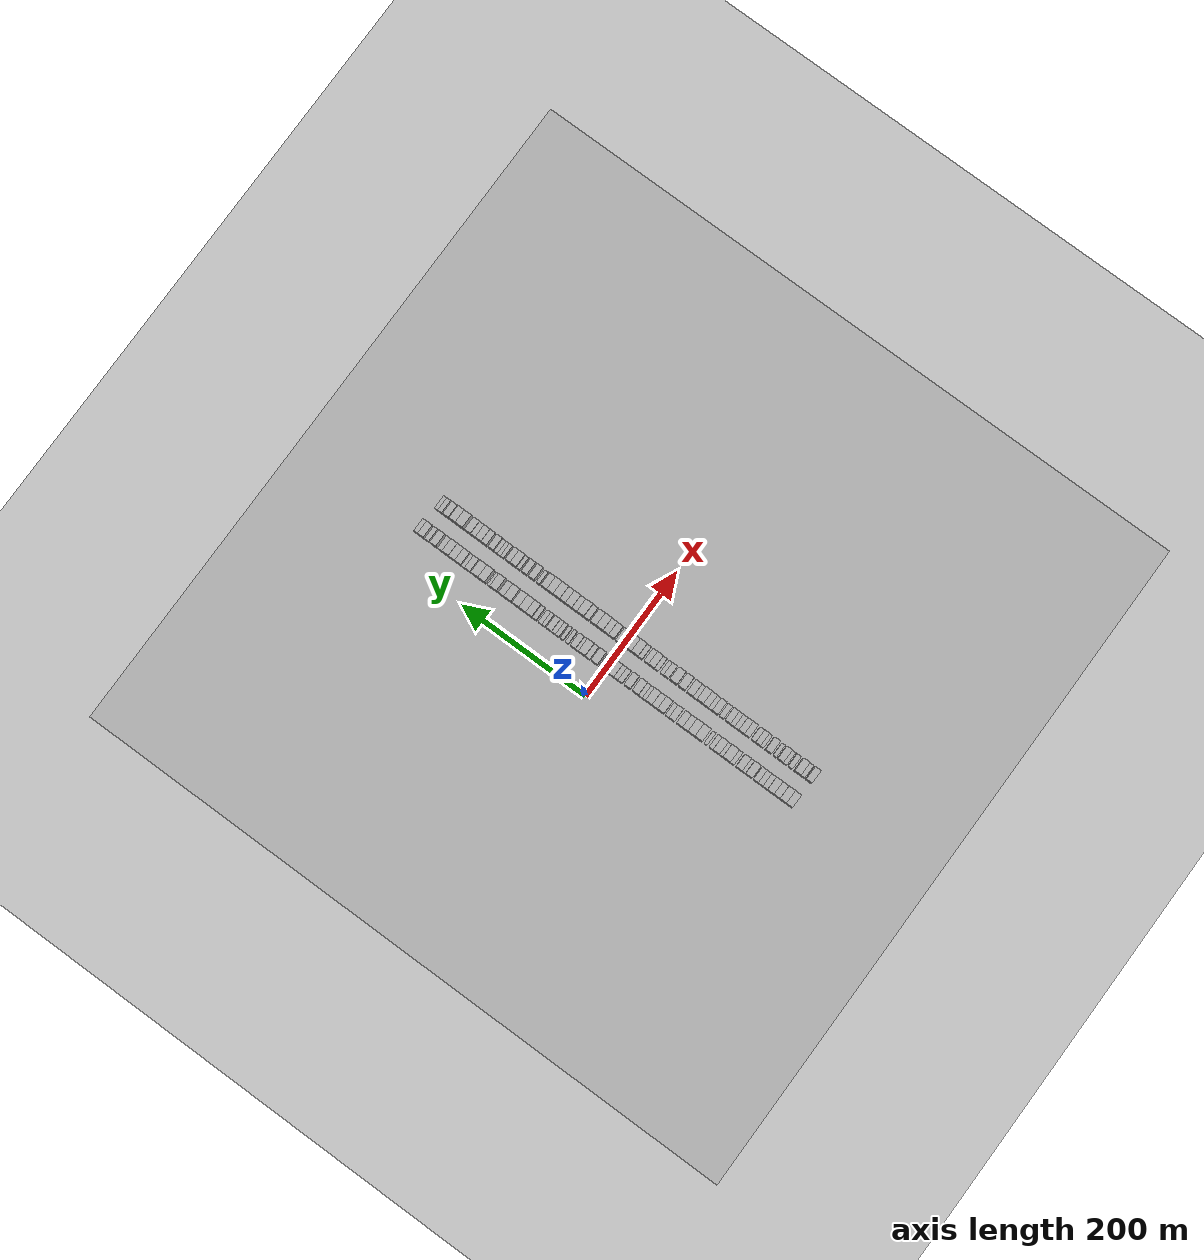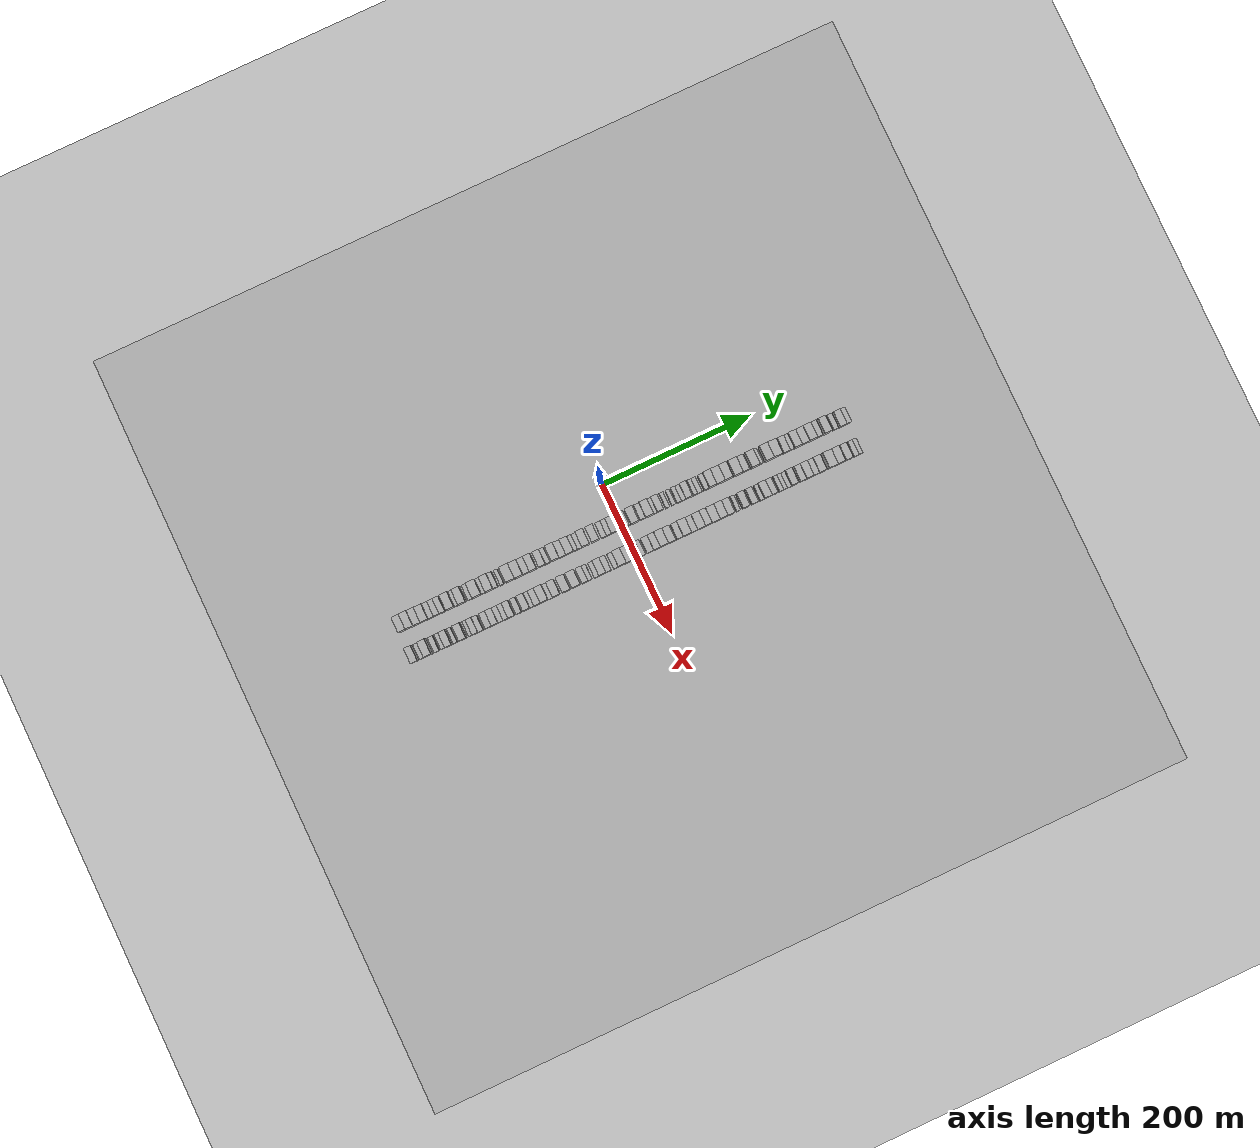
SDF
<?xml version="1.0" encoding="utf-8"?>

<sdf version="1.6">

   <world name="default">

      <gui fullscreen="0">

         <camera name="user_camera">

            <pose>-15 0 4.57585 0 0 0</pose>

            <view_controller>orbit</view_controller>

         </camera>

      </gui>

      <scene>

         <sky>

           <clouds>

             <speed>12</speed>

           </clouds>

         </sky>

         <ambient>0.4 0.4 0.4 1</ambient>

         <background>0.7 0.7 0.7 1</background>

         <shadows>1</shadows>

      </scene>

      <gravity>0 0 -9.8066</gravity>

      <magnetic_field>6e-06 2.3e-05 -4.2e-05</magnetic_field>

      <physics default="0" name="default_physics" type="ode">

         <ode>

            <solver>

               <type>quick</type>

               <iters>10</iters>

               <sor>1.0</sor>

               <use_dynamic_moi_rescaling>0</use_dynamic_moi_rescaling>

            </solver>

            <constraints>

               <cfm>0</cfm>

               <erp>0.2</erp>

               <contact_max_correcting_vel>100</contact_max_correcting_vel>

               <contact_surface_layer>0.001</contact_surface_layer>

            </constraints>

         </ode>

         <max_step_size>0.004</max_step_size>

         <real_time_factor>1</real_time_factor>

         <real_time_update_rate>250</real_time_update_rate>

      </physics>

      <light name="sun" type="directional">

         <cast_shadows>1</cast_shadows>

         <pose>0 0 10 0 0 0</pose>

         <diffuse>0.8 0.8 0.8 1</diffuse>

         <specular>0.2 0.2 0.2 1</specular>

         <attenuation>

            <range>1000</range>

            <constant>0.9</constant>

            <linear>0.01</linear>

            <quadratic>0.001</quadratic>

         </attenuation>

         <direction>-0.5 0.1 -0.9</direction>

      </light>

      <include>

         <name>ground_plane_1</name>

         <uri>model://HANNAS_ground_plane</uri>

         <pose>0 0 0  0 0 0</pose>

      </include>

      <include>

         <name>ground_plane_2</name>

         <uri>model://HANNAS_ground_plane</uri>

         <pose>100 0 0  0 0 0</pose>

      </include>

      <model name="building_1">

         <static>1</static>

         <pose frame="">50.0000 -293.0404 0 0.000000 0.000000 0.000000</pose>

         <link name="link">

            <pose frame="">0 0 10.50 0 0 0</pose>

            <collision name="collision">

               <geometry>

                  <box>

                     <size>20.0000 9.9192 21.0000</size>

                  </box>

               </geometry>

               <max_contacts>10</max_contacts>

               <surface>

                  <contact>

                     <ode/>

                  </contact>

                  <bounce/>

                  <friction>

                     <torsional>

                        <ode/>

                     </torsional>

                     <ode/>

                  </friction>

               </surface>

            </collision>

            <visual name="visual">

               <cast_shadows>0</cast_shadows>

               <geometry>

                  <box>

                     <size>20.0000 9.9192 21.0000</size>

                  </box>

               </geometry>

               <material>

                  <script>

                     <uri>model://HANNAS_wall/materials/scripts</uri>

                     <uri>model://HANNAS_wall/materials/textures</uri>

                     <name>vrc/HANNAS_wall</name>

                  </script>

               </material>

            </visual>

            <self_collide>0</self_collide>

            <enable_wind>0</enable_wind>

            <kinematic>0</kinematic>

         </link>

      </model>

      <model name="building_2">

         <static>1</static>

         <pose frame="">50.0000 -283.0995 0 0.000000 0.000000 0.000000</pose>

         <link name="link">

            <pose frame="">0 0 12.00 0 0 0</pose>

            <collision name="collision">

               <geometry>

                  <box>

                     <size>20.0000 9.9627 24.0000</size>

                  </box>

               </geometry>

               <max_contacts>10</max_contacts>

               <surface>

                  <contact>

                     <ode/>

                  </contact>

                  <bounce/>

                  <friction>

                     <torsional>

                        <ode/>

                     </torsional>

                     <ode/>

                  </friction>

               </surface>

            </collision>

            <visual name="visual">

               <cast_shadows>0</cast_shadows>

               <geometry>

                  <box>

                     <size>20.0000 9.9627 24.0000</size>

                  </box>

               </geometry>

               <material>

                  <script>

                     <uri>model://HANNAS_wall/materials/scripts</uri>

                     <uri>model://HANNAS_wall/materials/textures</uri>

                     <name>vrc/HANNAS_wall</name>

                  </script>

               </material>

            </visual>

            <self_collide>0</self_collide>

            <enable_wind>0</enable_wind>

            <kinematic>0</kinematic>

         </link>

      </model>

      <model name="building_3">

         <static>1</static>

         <pose frame="">50.0000 -273.4754 0 0.000000 0.000000 0.000000</pose>

         <link name="link">

            <pose frame="">0 0 10.50 0 0 0</pose>

            <collision name="collision">

               <geometry>

                  <box>

                     <size>20.0000 9.2853 21.0000</size>

                  </box>

               </geometry>

               <max_contacts>10</max_contacts>

               <surface>

                  <contact>

                     <ode/>

                  </contact>

                  <bounce/>

                  <friction>

                     <torsional>

                        <ode/>

                     </torsional>

                     <ode/>

                  </friction>

               </surface>

            </collision>

            <visual name="visual">

               <cast_shadows>0</cast_shadows>

               <geometry>

                  <box>

                     <size>20.0000 9.2853 21.0000</size>

                  </box>

               </geometry>

               <material>

                  <script>

                     <uri>model://HANNAS_wall/materials/scripts</uri>

                     <uri>model://HANNAS_wall/materials/textures</uri>

                     <name>vrc/HANNAS_wall</name>

                  </script>

               </material>

            </visual>

            <self_collide>0</self_collide>

            <enable_wind>0</enable_wind>

            <kinematic>0</kinematic>

         </link>

      </model>

      <model name="building_4">

         <static>1</static>

         <pose frame="">50.0000 -263.8147 0 0.000000 0.000000 0.000000</pose>

         <link name="link">

            <pose frame="">0 0 10.50 0 0 0</pose>

            <collision name="collision">

               <geometry>

                  <box>

                     <size>20.0000 10.0361 21.0000</size>

                  </box>

               </geometry>

               <max_contacts>10</max_contacts>

               <surface>

                  <contact>

                     <ode/>

                  </contact>

                  <bounce/>

                  <friction>

                     <torsional>

                        <ode/>

                     </torsional>

                     <ode/>

                  </friction>

               </surface>

            </collision>

            <visual name="visual">

               <cast_shadows>0</cast_shadows>

               <geometry>

                  <box>

                     <size>20.0000 10.0361 21.0000</size>

                  </box>

               </geometry>

               <material>

                  <script>

                     <uri>model://HANNAS_wall/materials/scripts</uri>

                     <uri>model://HANNAS_wall/materials/textures</uri>

                     <name>vrc/HANNAS_wall</name>

                  </script>

               </material>

            </visual>

            <self_collide>0</self_collide>

            <enable_wind>0</enable_wind>

            <kinematic>0</kinematic>

         </link>

      </model>

      <model name="building_5">

         <static>1</static>

         <pose frame="">50.0000 -255.1313 0 0.000000 0.000000 0.000000</pose>

         <link name="link">

            <pose frame="">0 0 7.50 0 0 0</pose>

            <collision name="collision">

               <geometry>

                  <box>

                     <size>20.0000 7.3308 15.0000</size>

                  </box>

               </geometry>

               <max_contacts>10</max_contacts>

               <surface>

                  <contact>

                     <ode/>

                  </contact>

                  <bounce/>

                  <friction>

                     <torsional>

                        <ode/>

                     </torsional>

                     <ode/>

                  </friction>

               </surface>

            </collision>

            <visual name="visual">

               <cast_shadows>0</cast_shadows>

               <geometry>

                  <box>

                     <size>20.0000 7.3308 15.0000</size>

                  </box>

               </geometry>

               <material>

                  <script>

                     <uri>model://HANNAS_wall/materials/scripts</uri>

                     <uri>model://HANNAS_wall/materials/textures</uri>

                     <name>vrc/HANNAS_wall</name>

                  </script>

               </material>

            </visual>

            <self_collide>0</self_collide>

            <enable_wind>0</enable_wind>

            <kinematic>0</kinematic>

         </link>

      </model>

      <model name="building_6">

         <static>1</static>

         <pose frame="">50.0000 -247.8303 0 0.000000 0.000000 0.000000</pose>

         <link name="link">

            <pose frame="">0 0 9.00 0 0 0</pose>

            <collision name="collision">

               <geometry>

                  <box>

                     <size>20.0000 7.2713 18.0000</size>

                  </box>

               </geometry>

               <max_contacts>10</max_contacts>

               <surface>

                  <contact>

                     <ode/>

                  </contact>

                  <bounce/>

                  <friction>

                     <torsional>

                        <ode/>

                     </torsional>

                     <ode/>

                  </friction>

               </surface>

            </collision>

            <visual name="visual">

               <cast_shadows>0</cast_shadows>

               <geometry>

                  <box>

                     <size>20.0000 7.2713 18.0000</size>

                  </box>

               </geometry>

               <material>

                  <script>

                     <uri>model://HANNAS_wall/materials/scripts</uri>

                     <uri>model://HANNAS_wall/materials/textures</uri>

                     <name>vrc/HANNAS_wall</name>

                  </script>

               </material>

            </visual>

            <self_collide>0</self_collide>

            <enable_wind>0</enable_wind>

            <kinematic>0</kinematic>

         </link>

      </model>

      <model name="building_7">

         <static>1</static>

         <pose frame="">50.0000 -240.4107 0 0.000000 0.000000 0.000000</pose>

         <link name="link">

            <pose frame="">0 0 9.00 0 0 0</pose>

            <collision name="collision">

               <geometry>

                  <box>

                     <size>20.0000 7.5679 18.0000</size>

                  </box>

               </geometry>

               <max_contacts>10</max_contacts>

               <surface>

                  <contact>

                     <ode/>

                  </contact>

                  <bounce/>

                  <friction>

                     <torsional>

                        <ode/>

                     </torsional>

                     <ode/>

                  </friction>

               </surface>

            </collision>

            <visual name="visual">

               <cast_shadows>0</cast_shadows>

               <geometry>

                  <box>

                     <size>20.0000 7.5679 18.0000</size>

                  </box>

               </geometry>

               <material>

                  <script>

                     <uri>model://HANNAS_wall/materials/scripts</uri>

                     <uri>model://HANNAS_wall/materials/textures</uri>

                     <name>vrc/HANNAS_wall</name>

                  </script>

               </material>

            </visual>

            <self_collide>0</self_collide>

            <enable_wind>0</enable_wind>

            <kinematic>0</kinematic>

         </link>

      </model>

      <model name="building_8">

         <static>1</static>

         <pose frame="">50.0000 -229.4162 0 0.000000 0.000000 0.000000</pose>

         <link name="link">

            <pose frame="">0 0 12.00 0 0 0</pose>

            <collision name="collision">

               <geometry>

                  <box>

                     <size>20.0000 10.4211 24.0000</size>

                  </box>

               </geometry>

               <max_contacts>10</max_contacts>

               <surface>

                  <contact>

                     <ode/>

                  </contact>

                  <bounce/>

                  <friction>

                     <torsional>

                        <ode/>

                     </torsional>

                     <ode/>

                  </friction>

               </surface>

            </collision>

            <visual name="visual">

               <cast_shadows>0</cast_shadows>

               <geometry>

                  <box>

                     <size>20.0000 10.4211 24.0000</size>

                  </box>

               </geometry>

               <material>

                  <script>

                     <uri>model://HANNAS_wall/materials/scripts</uri>

                     <uri>model://HANNAS_wall/materials/textures</uri>

                     <name>vrc/HANNAS_wall</name>

                  </script>

               </material>

            </visual>

            <self_collide>0</self_collide>

            <enable_wind>0</enable_wind>

            <kinematic>0</kinematic>

         </link>

      </model>

      <model name="building_9">

         <static>1</static>

         <pose frame="">50.0000 -221.6135 0 0.000000 0.000000 0.000000</pose>

         <link name="link">

            <pose frame="">0 0 6.00 0 0 0</pose>

            <collision name="collision">

               <geometry>

                  <box>

                     <size>20.0000 5.1843 12.0000</size>

                  </box>

               </geometry>

               <max_contacts>10</max_contacts>

               <surface>

                  <contact>

                     <ode/>

                  </contact>

                  <bounce/>

                  <friction>

                     <torsional>

                        <ode/>

                     </torsional>

                     <ode/>

                  </friction>

               </surface>

            </collision>

            <visual name="visual">

               <cast_shadows>0</cast_shadows>

               <geometry>

                  <box>

                     <size>20.0000 5.1843 12.0000</size>

                  </box>

               </geometry>

               <material>

                  <script>

                     <uri>model://HANNAS_wall/materials/scripts</uri>

                     <uri>model://HANNAS_wall/materials/textures</uri>

                     <name>vrc/HANNAS_wall</name>

                  </script>

               </material>

            </visual>

            <self_collide>0</self_collide>

            <enable_wind>0</enable_wind>

            <kinematic>0</kinematic>

         </link>

      </model>

      <model name="building_10">

         <static>1</static>

         <pose frame="">50.0000 -214.1070 0 0.000000 0.000000 0.000000</pose>

         <link name="link">

            <pose frame="">0 0 10.50 0 0 0</pose>

            <collision name="collision">

               <geometry>

                  <box>

                     <size>20.0000 9.8287 21.0000</size>

                  </box>

               </geometry>

               <max_contacts>10</max_contacts>

               <surface>

                  <contact>

                     <ode/>

                  </contact>

                  <bounce/>

                  <friction>

                     <torsional>

                        <ode/>

                     </torsional>

                     <ode/>

                  </friction>

               </surface>

            </collision>

            <visual name="visual">

               <cast_shadows>0</cast_shadows>

               <geometry>

                  <box>

                     <size>20.0000 9.8287 21.0000</size>

                  </box>

               </geometry>

               <material>

                  <script>

                     <uri>model://HANNAS_wall/materials/scripts</uri>

                     <uri>model://HANNAS_wall/materials/textures</uri>

                     <name>vrc/HANNAS_wall</name>

                  </script>

               </material>

            </visual>

            <self_collide>0</self_collide>

            <enable_wind>0</enable_wind>

            <kinematic>0</kinematic>

         </link>

      </model>

      <model name="building_11">

         <static>1</static>

         <pose frame="">50.0000 -203.1111 0 0.000000 0.000000 0.000000</pose>

         <link name="link">

            <pose frame="">0 0 7.50 0 0 0</pose>

            <collision name="collision">

               <geometry>

                  <box>

                     <size>20.0000 6.1631 15.0000</size>

                  </box>

               </geometry>

               <max_contacts>10</max_contacts>

               <surface>

                  <contact>

                     <ode/>

                  </contact>

                  <bounce/>

                  <friction>

                     <torsional>

                        <ode/>

                     </torsional>

                     <ode/>

                  </friction>

               </surface>

            </collision>

            <visual name="visual">

               <cast_shadows>0</cast_shadows>

               <geometry>

                  <box>

                     <size>20.0000 6.1631 15.0000</size>

                  </box>

               </geometry>

               <material>

                  <script>

                     <uri>model://HANNAS_wall/materials/scripts</uri>

                     <uri>model://HANNAS_wall/materials/textures</uri>

                     <name>vrc/HANNAS_wall</name>

                  </script>

               </material>

            </visual>

            <self_collide>0</self_collide>

            <enable_wind>0</enable_wind>

            <kinematic>0</kinematic>

         </link>

      </model>

      <model name="building_12">

         <static>1</static>

         <pose frame="">50.0000 -194.1699 0 0.000000 0.000000 0.000000</pose>

         <link name="link">

            <pose frame="">0 0 12.00 0 0 0</pose>

            <collision name="collision">

               <geometry>

                  <box>

                     <size>20.0000 11.7193 24.0000</size>

                  </box>

               </geometry>

               <max_contacts>10</max_contacts>

               <surface>

                  <contact>

                     <ode/>

                  </contact>

                  <bounce/>

                  <friction>

                     <torsional>

                        <ode/>

                     </torsional>

                     <ode/>

                  </friction>

               </surface>

            </collision>

            <visual name="visual">

               <cast_shadows>0</cast_shadows>

               <geometry>

                  <box>

                     <size>20.0000 11.7193 24.0000</size>

                  </box>

               </geometry>

               <material>

                  <script>

                     <uri>model://HANNAS_wall/materials/scripts</uri>

                     <uri>model://HANNAS_wall/materials/textures</uri>

                     <name>vrc/HANNAS_wall</name>

                  </script>

               </material>

            </visual>

            <self_collide>0</self_collide>

            <enable_wind>0</enable_wind>

            <kinematic>0</kinematic>

         </link>

      </model>

      <model name="building_13">

         <static>1</static>

         <pose frame="">50.0000 -185.6866 0 0.000000 0.000000 0.000000</pose>

         <link name="link">

            <pose frame="">0 0 6.00 0 0 0</pose>

            <collision name="collision">

               <geometry>

                  <box>

                     <size>20.0000 5.2473 12.0000</size>

                  </box>

               </geometry>

               <max_contacts>10</max_contacts>

               <surface>

                  <contact>

                     <ode/>

                  </contact>

                  <bounce/>

                  <friction>

                     <torsional>

                        <ode/>

                     </torsional>

                     <ode/>

                  </friction>

               </surface>

            </collision>

            <visual name="visual">

               <cast_shadows>0</cast_shadows>

               <geometry>

                  <box>

                     <size>20.0000 5.2473 12.0000</size>

                  </box>

               </geometry>

               <material>

                  <script>

                     <uri>model://HANNAS_wall/materials/scripts</uri>

                     <uri>model://HANNAS_wall/materials/textures</uri>

                     <name>vrc/HANNAS_wall</name>

                  </script>

               </material>

            </visual>

            <self_collide>0</self_collide>

            <enable_wind>0</enable_wind>

            <kinematic>0</kinematic>

         </link>

      </model>

      <model name="building_14">

         <static>1</static>

         <pose frame="">50.0000 -177.9145 0 0.000000 0.000000 0.000000</pose>

         <link name="link">

            <pose frame="">0 0 10.50 0 0 0</pose>

            <collision name="collision">

               <geometry>

                  <box>

                     <size>20.0000 10.2970 21.0000</size>

                  </box>

               </geometry>

               <max_contacts>10</max_contacts>

               <surface>

                  <contact>

                     <ode/>

                  </contact>

                  <bounce/>

                  <friction>

                     <torsional>

                        <ode/>

                     </torsional>

                     <ode/>

                  </friction>

               </surface>

            </collision>

            <visual name="visual">

               <cast_shadows>0</cast_shadows>

               <geometry>

                  <box>

                     <size>20.0000 10.2970 21.0000</size>

                  </box>

               </geometry>

               <material>

                  <script>

                     <uri>model://HANNAS_wall/materials/scripts</uri>

                     <uri>model://HANNAS_wall/materials/textures</uri>

                     <name>vrc/HANNAS_wall</name>

                  </script>

               </material>

            </visual>

            <self_collide>0</self_collide>

            <enable_wind>0</enable_wind>

            <kinematic>0</kinematic>

         </link>

      </model>

      <model name="building_15">

         <static>1</static>

         <pose frame="">50.0000 -169.6922 0 0.000000 0.000000 0.000000</pose>

         <link name="link">

            <pose frame="">0 0 7.50 0 0 0</pose>

            <collision name="collision">

               <geometry>

                  <box>

                     <size>20.0000 6.1476 15.0000</size>

                  </box>

               </geometry>

               <max_contacts>10</max_contacts>

               <surface>

                  <contact>

                     <ode/>

                  </contact>

                  <bounce/>

                  <friction>

                     <torsional>

                        <ode/>

                     </torsional>

                     <ode/>

                  </friction>

               </surface>

            </collision>

            <visual name="visual">

               <cast_shadows>0</cast_shadows>

               <geometry>

                  <box>

                     <size>20.0000 6.1476 15.0000</size>

                  </box>

               </geometry>

               <material>

                  <script>

                     <uri>model://HANNAS_wall/materials/scripts</uri>

                     <uri>model://HANNAS_wall/materials/textures</uri>

                     <name>vrc/HANNAS_wall</name>

                  </script>

               </material>

            </visual>

            <self_collide>0</self_collide>

            <enable_wind>0</enable_wind>

            <kinematic>0</kinematic>

         </link>

      </model>

      <model name="building_16">

         <static>1</static>

         <pose frame="">50.0000 -161.1644 0 0.000000 0.000000 0.000000</pose>

         <link name="link">

            <pose frame="">0 0 6.00 0 0 0</pose>

            <collision name="collision">

               <geometry>

                  <box>

                     <size>20.0000 4.9079 12.0000</size>

                  </box>

               </geometry>

               <max_contacts>10</max_contacts>

               <surface>

                  <contact>

                     <ode/>

                  </contact>

                  <bounce/>

                  <friction>

                     <torsional>

                        <ode/>

                     </torsional>

                     <ode/>

                  </friction>

               </surface>

            </collision>

            <visual name="visual">

               <cast_shadows>0</cast_shadows>

               <geometry>

                  <box>

                     <size>20.0000 4.9079 12.0000</size>

                  </box>

               </geometry>

               <material>

                  <script>

                     <uri>model://HANNAS_wall/materials/scripts</uri>

                     <uri>model://HANNAS_wall/materials/textures</uri>

                     <name>vrc/HANNAS_wall</name>

                  </script>

               </material>

            </visual>

            <self_collide>0</self_collide>

            <enable_wind>0</enable_wind>

            <kinematic>0</kinematic>

         </link>

      </model>

      <model name="building_17">

         <static>1</static>

         <pose frame="">50.0000 -149.8009 0 0.000000 0.000000 0.000000</pose>

         <link name="link">

            <pose frame="">0 0 12.00 0 0 0</pose>

            <collision name="collision">

               <geometry>

                  <box>

                     <size>20.0000 11.8191 24.0000</size>

                  </box>

               </geometry>

               <max_contacts>10</max_contacts>

               <surface>

                  <contact>

                     <ode/>

                  </contact>

                  <bounce/>

                  <friction>

                     <torsional>

                        <ode/>

                     </torsional>

                     <ode/>

                  </friction>

               </surface>

            </collision>

            <visual name="visual">

               <cast_shadows>0</cast_shadows>

               <geometry>

                  <box>

                     <size>20.0000 11.8191 24.0000</size>

                  </box>

               </geometry>

               <material>

                  <script>

                     <uri>model://HANNAS_wall/materials/scripts</uri>

                     <uri>model://HANNAS_wall/materials/textures</uri>

                     <name>vrc/HANNAS_wall</name>

                  </script>

               </material>

            </visual>

            <self_collide>0</self_collide>

            <enable_wind>0</enable_wind>

            <kinematic>0</kinematic>

         </link>

      </model>

      <model name="building_18">

         <static>1</static>

         <pose frame="">50.0000 -138.4631 0 0.000000 0.000000 0.000000</pose>

         <link name="link">

            <pose frame="">0 0 12.00 0 0 0</pose>

            <collision name="collision">

               <geometry>

                  <box>

                     <size>20.0000 10.8565 24.0000</size>

                  </box>

               </geometry>

               <max_contacts>10</max_contacts>

               <surface>

                  <contact>

                     <ode/>

                  </contact>

                  <bounce/>

                  <friction>

                     <torsional>

                        <ode/>

                     </torsional>

                     <ode/>

                  </friction>

               </surface>

            </collision>

            <visual name="visual">

               <cast_shadows>0</cast_shadows>

               <geometry>

                  <box>

                     <size>20.0000 10.8565 24.0000</size>

                  </box>

               </geometry>

               <material>

                  <script>

                     <uri>model://HANNAS_wall/materials/scripts</uri>

                     <uri>model://HANNAS_wall/materials/textures</uri>

                     <name>vrc/HANNAS_wall</name>

                  </script>

               </material>

            </visual>

            <self_collide>0</self_collide>

            <enable_wind>0</enable_wind>

            <kinematic>0</kinematic>

         </link>

      </model>

      <model name="building_19">

         <static>1</static>

         <pose frame="">50.0000 -128.7146 0 0.000000 0.000000 0.000000</pose>

         <link name="link">

            <pose frame="">0 0 9.00 0 0 0</pose>

            <collision name="collision">

               <geometry>

                  <box>

                     <size>20.0000 8.6404 18.0000</size>

                  </box>

               </geometry>

               <max_contacts>10</max_contacts>

               <surface>

                  <contact>

                     <ode/>

                  </contact>

                  <bounce/>

                  <friction>

                     <torsional>

                        <ode/>

                     </torsional>

                     <ode/>

                  </friction>

               </surface>

            </collision>

            <visual name="visual">

               <cast_shadows>0</cast_shadows>

               <geometry>

                  <box>

                     <size>20.0000 8.6404 18.0000</size>

                  </box>

               </geometry>

               <material>

                  <script>

                     <uri>model://HANNAS_wall/materials/scripts</uri>

                     <uri>model://HANNAS_wall/materials/textures</uri>

                     <name>vrc/HANNAS_wall</name>

                  </script>

               </material>

            </visual>

            <self_collide>0</self_collide>

            <enable_wind>0</enable_wind>

            <kinematic>0</kinematic>

         </link>

      </model>

      <model name="building_20">

         <static>1</static>

         <pose frame="">50.0000 -119.7162 0 0.000000 0.000000 0.000000</pose>

         <link name="link">

            <pose frame="">0 0 10.50 0 0 0</pose>

            <collision name="collision">

               <geometry>

                  <box>

                     <size>20.0000 9.3563 21.0000</size>

                  </box>

               </geometry>

               <max_contacts>10</max_contacts>

               <surface>

                  <contact>

                     <ode/>

                  </contact>

                  <bounce/>

                  <friction>

                     <torsional>

                        <ode/>

                     </torsional>

                     <ode/>

                  </friction>

               </surface>

            </collision>

            <visual name="visual">

               <cast_shadows>0</cast_shadows>

               <geometry>

                  <box>

                     <size>20.0000 9.3563 21.0000</size>

                  </box>

               </geometry>

               <material>

                  <script>

                     <uri>model://HANNAS_wall/materials/scripts</uri>

                     <uri>model://HANNAS_wall/materials/textures</uri>

                     <name>vrc/HANNAS_wall</name>

                  </script>

               </material>

            </visual>

            <self_collide>0</self_collide>

            <enable_wind>0</enable_wind>

            <kinematic>0</kinematic>

         </link>

      </model>

      <model name="building_21">

         <static>1</static>

         <pose frame="">50.0000 -107.5606 0 0.000000 0.000000 0.000000</pose>

         <link name="link">

            <pose frame="">0 0 10.50 0 0 0</pose>

            <collision name="collision">

               <geometry>

                  <box>

                     <size>20.0000 8.9550 21.0000</size>

                  </box>

               </geometry>

               <max_contacts>10</max_contacts>

               <surface>

                  <contact>

                     <ode/>

                  </contact>

                  <bounce/>

                  <friction>

                     <torsional>

                        <ode/>

                     </torsional>

                     <ode/>

                  </friction>

               </surface>

            </collision>

            <visual name="visual">

               <cast_shadows>0</cast_shadows>

               <geometry>

                  <box>

                     <size>20.0000 8.9550 21.0000</size>

                  </box>

               </geometry>

               <material>

                  <script>

                     <uri>model://HANNAS_wall/materials/scripts</uri>

                     <uri>model://HANNAS_wall/materials/textures</uri>

                     <name>vrc/HANNAS_wall</name>

                  </script>

               </material>

            </visual>

            <self_collide>0</self_collide>

            <enable_wind>0</enable_wind>

            <kinematic>0</kinematic>

         </link>

      </model>

      <model name="building_22">

         <static>1</static>

         <pose frame="">50.0000 -100.0929 0 0.000000 0.000000 0.000000</pose>

         <link name="link">

            <pose frame="">0 0 6.00 0 0 0</pose>

            <collision name="collision">

               <geometry>

                  <box>

                     <size>20.0000 5.9805 12.0000</size>

                  </box>

               </geometry>

               <max_contacts>10</max_contacts>

               <surface>

                  <contact>

                     <ode/>

                  </contact>

                  <bounce/>

                  <friction>

                     <torsional>

                        <ode/>

                     </torsional>

                     <ode/>

                  </friction>

               </surface>

            </collision>

            <visual name="visual">

               <cast_shadows>0</cast_shadows>

               <geometry>

                  <box>

                     <size>20.0000 5.9805 12.0000</size>

                  </box>

               </geometry>

               <material>

                  <script>

                     <uri>model://HANNAS_wall/materials/scripts</uri>

                     <uri>model://HANNAS_wall/materials/textures</uri>

                     <name>vrc/HANNAS_wall</name>

                  </script>

               </material>

            </visual>

            <self_collide>0</self_collide>

            <enable_wind>0</enable_wind>

            <kinematic>0</kinematic>

         </link>

      </model>

      <model name="building_23">

         <static>1</static>

         <pose frame="">50.0000 -89.9068 0 0.000000 0.000000 0.000000</pose>

         <link name="link">

            <pose frame="">0 0 12.00 0 0 0</pose>

            <collision name="collision">

               <geometry>

                  <box>

                     <size>20.0000 10.3917 24.0000</size>

                  </box>

               </geometry>

               <max_contacts>10</max_contacts>

               <surface>

                  <contact>

                     <ode/>

                  </contact>

                  <bounce/>

                  <friction>

                     <torsional>

                        <ode/>

                     </torsional>

                     <ode/>

                  </friction>

               </surface>

            </collision>

            <visual name="visual">

               <cast_shadows>0</cast_shadows>

               <geometry>

                  <box>

                     <size>20.0000 10.3917 24.0000</size>

                  </box>

               </geometry>

               <material>

                  <script>

                     <uri>model://HANNAS_wall/materials/scripts</uri>

                     <uri>model://HANNAS_wall/materials/textures</uri>

                     <name>vrc/HANNAS_wall</name>

                  </script>

               </material>

            </visual>

            <self_collide>0</self_collide>

            <enable_wind>0</enable_wind>

            <kinematic>0</kinematic>

         </link>

      </model>

      <model name="building_24">

         <static>1</static>

         <pose frame="">50.0000 -80.3440 0 0.000000 0.000000 0.000000</pose>

         <link name="link">

            <pose frame="">0 0 9.00 0 0 0</pose>

            <collision name="collision">

               <geometry>

                  <box>

                     <size>20.0000 8.7340 18.0000</size>

                  </box>

               </geometry>

               <max_contacts>10</max_contacts>

               <surface>

                  <contact>

                     <ode/>

                  </contact>

                  <bounce/>

                  <friction>

                     <torsional>

                        <ode/>

                     </torsional>

                     <ode/>

                  </friction>

               </surface>

            </collision>

            <visual name="visual">

               <cast_shadows>0</cast_shadows>

               <geometry>

                  <box>

                     <size>20.0000 8.7340 18.0000</size>

                  </box>

               </geometry>

               <material>

                  <script>

                     <uri>model://HANNAS_wall/materials/scripts</uri>

                     <uri>model://HANNAS_wall/materials/textures</uri>

                     <name>vrc/HANNAS_wall</name>

                  </script>

               </material>

            </visual>

            <self_collide>0</self_collide>

            <enable_wind>0</enable_wind>

            <kinematic>0</kinematic>

         </link>

      </model>

      <model name="building_25">

         <static>1</static>

         <pose frame="">50.0000 -70.8512 0 0.000000 0.000000 0.000000</pose>

         <link name="link">

            <pose frame="">0 0 10.50 0 0 0</pose>

            <collision name="collision">

               <geometry>

                  <box>

                     <size>20.0000 10.2515 21.0000</size>

                  </box>

               </geometry>

               <max_contacts>10</max_contacts>

               <surface>

                  <contact>

                     <ode/>

                  </contact>

                  <bounce/>

                  <friction>

                     <torsional>

                        <ode/>

                     </torsional>

                     <ode/>

                  </friction>

               </surface>

            </collision>

            <visual name="visual">

               <cast_shadows>0</cast_shadows>

               <geometry>

                  <box>

                     <size>20.0000 10.2515 21.0000</size>

                  </box>

               </geometry>

               <material>

                  <script>

                     <uri>model://HANNAS_wall/materials/scripts</uri>

                     <uri>model://HANNAS_wall/materials/textures</uri>

                     <name>vrc/HANNAS_wall</name>

                  </script>

               </material>

            </visual>

            <self_collide>0</self_collide>

            <enable_wind>0</enable_wind>

            <kinematic>0</kinematic>

         </link>

      </model>

      <model name="building_26">

         <static>1</static>

         <pose frame="">50.0000 -63.0987 0 0.000000 0.000000 0.000000</pose>

         <link name="link">

            <pose frame="">0 0 6.00 0 0 0</pose>

            <collision name="collision">

               <geometry>

                  <box>

                     <size>20.0000 5.2537 12.0000</size>

                  </box>

               </geometry>

               <max_contacts>10</max_contacts>

               <surface>

                  <contact>

                     <ode/>

                  </contact>

                  <bounce/>

                  <friction>

                     <torsional>

                        <ode/>

                     </torsional>

                     <ode/>

                  </friction>

               </surface>

            </collision>

            <visual name="visual">

               <cast_shadows>0</cast_shadows>

               <geometry>

                  <box>

                     <size>20.0000 5.2537 12.0000</size>

                  </box>

               </geometry>

               <material>

                  <script>

                     <uri>model://HANNAS_wall/materials/scripts</uri>

                     <uri>model://HANNAS_wall/materials/textures</uri>

                     <name>vrc/HANNAS_wall</name>

                  </script>

               </material>

            </visual>

            <self_collide>0</self_collide>

            <enable_wind>0</enable_wind>

            <kinematic>0</kinematic>

         </link>

      </model>

      <model name="building_27">

         <static>1</static>

         <pose frame="">50.0000 -57.5809 0 0.000000 0.000000 0.000000</pose>

         <link name="link">

            <pose frame="">0 0 6.00 0 0 0</pose>

            <collision name="collision">

               <geometry>

                  <box>

                     <size>20.0000 5.7818 12.0000</size>

                  </box>

               </geometry>

               <max_contacts>10</max_contacts>

               <surface>

                  <contact>

                     <ode/>

                  </contact>

                  <bounce/>

                  <friction>

                     <torsional>

                        <ode/>

                     </torsional>

                     <ode/>

                  </friction>

               </surface>

            </collision>

            <visual name="visual">

               <cast_shadows>0</cast_shadows>

               <geometry>

                  <box>

                     <size>20.0000 5.7818 12.0000</size>

                  </box>

               </geometry>

               <material>

                  <script>

                     <uri>model://HANNAS_wall/materials/scripts</uri>

                     <uri>model://HANNAS_wall/materials/textures</uri>

                     <name>vrc/HANNAS_wall</name>

                  </script>

               </material>

            </visual>

            <self_collide>0</self_collide>

            <enable_wind>0</enable_wind>

            <kinematic>0</kinematic>

         </link>

      </model>

      <model name="building_28">

         <static>1</static>

         <pose frame="">50.0000 -49.6364 0 0.000000 0.000000 0.000000</pose>

         <link name="link">

            <pose frame="">0 0 12.00 0 0 0</pose>

            <collision name="collision">

               <geometry>

                  <box>

                     <size>20.0000 10.1071 24.0000</size>

                  </box>

               </geometry>

               <max_contacts>10</max_contacts>

               <surface>

                  <contact>

                     <ode/>

                  </contact>

                  <bounce/>

                  <friction>

                     <torsional>

                        <ode/>

                     </torsional>

                     <ode/>

                  </friction>

               </surface>

            </collision>

            <visual name="visual">

               <cast_shadows>0</cast_shadows>

               <geometry>

                  <box>

                     <size>20.0000 10.1071 24.0000</size>

                  </box>

               </geometry>

               <material>

                  <script>

                     <uri>model://HANNAS_wall/materials/scripts</uri>

                     <uri>model://HANNAS_wall/materials/textures</uri>

                     <name>vrc/HANNAS_wall</name>

                  </script>

               </material>

            </visual>

            <self_collide>0</self_collide>

            <enable_wind>0</enable_wind>

            <kinematic>0</kinematic>

         </link>

      </model>

      <model name="building_29">

         <static>1</static>

         <pose frame="">50.0000 -36.6501 0 0.000000 0.000000 0.000000</pose>

         <link name="link">

            <pose frame="">0 0 12.00 0 0 0</pose>

            <collision name="collision">

               <geometry>

                  <box>

                     <size>20.0000 9.8655 24.0000</size>

                  </box>

               </geometry>

               <max_contacts>10</max_contacts>

               <surface>

                  <contact>

                     <ode/>

                  </contact>

                  <bounce/>

                  <friction>

                     <torsional>

                        <ode/>

                     </torsional>

                     <ode/>

                  </friction>

               </surface>

            </collision>

            <visual name="visual">

               <cast_shadows>0</cast_shadows>

               <geometry>

                  <box>

                     <size>20.0000 9.8655 24.0000</size>

                  </box>

               </geometry>

               <material>

                  <script>

                     <uri>model://HANNAS_wall/materials/scripts</uri>

                     <uri>model://HANNAS_wall/materials/textures</uri>

                     <name>vrc/HANNAS_wall</name>

                  </script>

               </material>

            </visual>

            <self_collide>0</self_collide>

            <enable_wind>0</enable_wind>

            <kinematic>0</kinematic>

         </link>

      </model>

      <model name="building_30">

         <static>1</static>

         <pose frame="">50.0000 -25.2569 0 0.000000 0.000000 0.000000</pose>

         <link name="link">

            <pose frame="">0 0 7.50 0 0 0</pose>

            <collision name="collision">

               <geometry>

                  <box>

                     <size>20.0000 6.9210 15.0000</size>

                  </box>

               </geometry>

               <max_contacts>10</max_contacts>

               <surface>

                  <contact>

                     <ode/>

                  </contact>

                  <bounce/>

                  <friction>

                     <torsional>

                        <ode/>

                     </torsional>

                     <ode/>

                  </friction>

               </surface>

            </collision>

            <visual name="visual">

               <cast_shadows>0</cast_shadows>

               <geometry>

                  <box>

                     <size>20.0000 6.9210 15.0000</size>

                  </box>

               </geometry>

               <material>

                  <script>

                     <uri>model://HANNAS_wall/materials/scripts</uri>

                     <uri>model://HANNAS_wall/materials/textures</uri>

                     <name>vrc/HANNAS_wall</name>

                  </script>

               </material>

            </visual>

            <self_collide>0</self_collide>

            <enable_wind>0</enable_wind>

            <kinematic>0</kinematic>

         </link>

      </model>

      <model name="building_31">

         <static>1</static>

         <pose frame="">50.0000 -18.5693 0 0.000000 0.000000 0.000000</pose>

         <link name="link">

            <pose frame="">0 0 7.50 0 0 0</pose>

            <collision name="collision">

               <geometry>

                  <box>

                     <size>20.0000 6.4541 15.0000</size>

                  </box>

               </geometry>

               <max_contacts>10</max_contacts>

               <surface>

                  <contact>

                     <ode/>

                  </contact>

                  <bounce/>

                  <friction>

                     <torsional>

                        <ode/>

                     </torsional>

                     <ode/>

                  </friction>

               </surface>

            </collision>

            <visual name="visual">

               <cast_shadows>0</cast_shadows>

               <geometry>

                  <box>

                     <size>20.0000 6.4541 15.0000</size>

                  </box>

               </geometry>

               <material>

                  <script>

                     <uri>model://HANNAS_wall/materials/scripts</uri>

                     <uri>model://HANNAS_wall/materials/textures</uri>

                     <name>vrc/HANNAS_wall</name>

                  </script>

               </material>

            </visual>

            <self_collide>0</self_collide>

            <enable_wind>0</enable_wind>

            <kinematic>0</kinematic>

         </link>

      </model>

      <model name="building_32">

         <static>1</static>

         <pose frame="">50.0000 -10.8621 0 0.000000 0.000000 0.000000</pose>

         <link name="link">

            <pose frame="">0 0 9.00 0 0 0</pose>

            <collision name="collision">

               <geometry>

                  <box>

                     <size>20.0000 8.9603 18.0000</size>

                  </box>

               </geometry>

               <max_contacts>10</max_contacts>

               <surface>

                  <contact>

                     <ode/>

                  </contact>

                  <bounce/>

                  <friction>

                     <torsional>

                        <ode/>

                     </torsional>

                     <ode/>

                  </friction>

               </surface>

            </collision>

            <visual name="visual">

               <cast_shadows>0</cast_shadows>

               <geometry>

                  <box>

                     <size>20.0000 8.9603 18.0000</size>

                  </box>

               </geometry>

               <material>

                  <script>

                     <uri>model://HANNAS_wall/materials/scripts</uri>

                     <uri>model://HANNAS_wall/materials/textures</uri>

                     <name>vrc/HANNAS_wall</name>

                  </script>

               </material>

            </visual>

            <self_collide>0</self_collide>

            <enable_wind>0</enable_wind>

            <kinematic>0</kinematic>

         </link>

      </model>

      <model name="building_33">

         <static>1</static>

         <pose frame="">50.0000 -2.5638 0 0.000000 0.000000 0.000000</pose>

         <link name="link">

            <pose frame="">0 0 9.00 0 0 0</pose>

            <collision name="collision">

               <geometry>

                  <box>

                     <size>20.0000 7.6363 18.0000</size>

                  </box>

               </geometry>

               <max_contacts>10</max_contacts>

               <surface>

                  <contact>

                     <ode/>

                  </contact>

                  <bounce/>

                  <friction>

                     <torsional>

                        <ode/>

                     </torsional>

                     <ode/>

                  </friction>

               </surface>

            </collision>

            <visual name="visual">

               <cast_shadows>0</cast_shadows>

               <geometry>

                  <box>

                     <size>20.0000 7.6363 18.0000</size>

                  </box>

               </geometry>

               <material>

                  <script>

                     <uri>model://HANNAS_wall/materials/scripts</uri>

                     <uri>model://HANNAS_wall/materials/textures</uri>

                     <name>vrc/HANNAS_wall</name>

                  </script>

               </material>

            </visual>

            <self_collide>0</self_collide>

            <enable_wind>0</enable_wind>

            <kinematic>0</kinematic>

         </link>

      </model>

      <model name="building_34">

         <static>1</static>

         <pose frame="">50.0000 5.9958 0 0.000000 0.000000 0.000000</pose>

         <link name="link">

            <pose frame="">0 0 6.00 0 0 0</pose>

            <collision name="collision">

               <geometry>

                  <box>

                     <size>20.0000 5.4830 12.0000</size>

                  </box>

               </geometry>

               <max_contacts>10</max_contacts>

               <surface>

                  <contact>

                     <ode/>

                  </contact>

                  <bounce/>

                  <friction>

                     <torsional>

                        <ode/>

                     </torsional>

                     <ode/>

                  </friction>

               </surface>

            </collision>

            <visual name="visual">

               <cast_shadows>0</cast_shadows>

               <geometry>

                  <box>

                     <size>20.0000 5.4830 12.0000</size>

                  </box>

               </geometry>

               <material>

                  <script>

                     <uri>model://HANNAS_wall/materials/scripts</uri>

                     <uri>model://HANNAS_wall/materials/textures</uri>

                     <name>vrc/HANNAS_wall</name>

                  </script>

               </material>

            </visual>

            <self_collide>0</self_collide>

            <enable_wind>0</enable_wind>

            <kinematic>0</kinematic>

         </link>

      </model>

      <model name="building_35">

         <static>1</static>

         <pose frame="">50.0000 15.9093 0 0.000000 0.000000 0.000000</pose>

         <link name="link">

            <pose frame="">0 0 12.00 0 0 0</pose>

            <collision name="collision">

               <geometry>

                  <box>

                     <size>20.0000 10.3439 24.0000</size>

                  </box>

               </geometry>

               <max_contacts>10</max_contacts>

               <surface>

                  <contact>

                     <ode/>

                  </contact>

                  <bounce/>

                  <friction>

                     <torsional>

                        <ode/>

                     </torsional>

                     <ode/>

                  </friction>

               </surface>

            </collision>

            <visual name="visual">

               <cast_shadows>0</cast_shadows>

               <geometry>

                  <box>

                     <size>20.0000 10.3439 24.0000</size>

                  </box>

               </geometry>

               <material>

                  <script>

                     <uri>model://HANNAS_wall/materials/scripts</uri>

                     <uri>model://HANNAS_wall/materials/textures</uri>

                     <name>vrc/HANNAS_wall</name>

                  </script>

               </material>

            </visual>

            <self_collide>0</self_collide>

            <enable_wind>0</enable_wind>

            <kinematic>0</kinematic>

         </link>

      </model>

      <model name="building_36">

         <static>1</static>

         <pose frame="">50.0000 26.6475 0 0.000000 0.000000 0.000000</pose>

         <link name="link">

            <pose frame="">0 0 7.50 0 0 0</pose>

            <collision name="collision">

               <geometry>

                  <box>

                     <size>20.0000 7.1325 15.0000</size>

                  </box>

               </geometry>

               <max_contacts>10</max_contacts>

               <surface>

                  <contact>

                     <ode/>

                  </contact>

                  <bounce/>

                  <friction>

                     <torsional>

                        <ode/>

                     </torsional>

                     <ode/>

                  </friction>

               </surface>

            </collision>

            <visual name="visual">

               <cast_shadows>0</cast_shadows>

               <geometry>

                  <box>

                     <size>20.0000 7.1325 15.0000</size>

                  </box>

               </geometry>

               <material>

                  <script>

                     <uri>model://HANNAS_wall/materials/scripts</uri>

                     <uri>model://HANNAS_wall/materials/textures</uri>

                     <name>vrc/HANNAS_wall</name>

                  </script>

               </material>

            </visual>

            <self_collide>0</self_collide>

            <enable_wind>0</enable_wind>

            <kinematic>0</kinematic>

         </link>

      </model>

      <model name="building_37">

         <static>1</static>

         <pose frame="">50.0000 35.5171 0 0.000000 0.000000 0.000000</pose>

         <link name="link">

            <pose frame="">0 0 12.00 0 0 0</pose>

            <collision name="collision">

               <geometry>

                  <box>

                     <size>20.0000 10.6068 24.0000</size>

                  </box>

               </geometry>

               <max_contacts>10</max_contacts>

               <surface>

                  <contact>

                     <ode/>

                  </contact>

                  <bounce/>

                  <friction>

                     <torsional>

                        <ode/>

                     </torsional>

                     <ode/>

                  </friction>

               </surface>

            </collision>

            <visual name="visual">

               <cast_shadows>0</cast_shadows>

               <geometry>

                  <box>

                     <size>20.0000 10.6068 24.0000</size>

                  </box>

               </geometry>

               <material>

                  <script>

                     <uri>model://HANNAS_wall/materials/scripts</uri>

                     <uri>model://HANNAS_wall/materials/textures</uri>

                     <name>vrc/HANNAS_wall</name>

                  </script>

               </material>

            </visual>

            <self_collide>0</self_collide>

            <enable_wind>0</enable_wind>

            <kinematic>0</kinematic>

         </link>

      </model>

      <model name="building_38">

         <static>1</static>

         <pose frame="">50.0000 43.3631 0 0.000000 0.000000 0.000000</pose>

         <link name="link">

            <pose frame="">0 0 6.00 0 0 0</pose>

            <collision name="collision">

               <geometry>

                  <box>

                     <size>20.0000 5.0853 12.0000</size>

                  </box>

               </geometry>

               <max_contacts>10</max_contacts>

               <surface>

                  <contact>

                     <ode/>

                  </contact>

                  <bounce/>

                  <friction>

                     <torsional>

                        <ode/>

                     </torsional>

                     <ode/>

                  </friction>

               </surface>

            </collision>

            <visual name="visual">

               <cast_shadows>0</cast_shadows>

               <geometry>

                  <box>

                     <size>20.0000 5.0853 12.0000</size>

                  </box>

               </geometry>

               <material>

                  <script>

                     <uri>model://HANNAS_wall/materials/scripts</uri>

                     <uri>model://HANNAS_wall/materials/textures</uri>

                     <name>vrc/HANNAS_wall</name>

                  </script>

               </material>

            </visual>

            <self_collide>0</self_collide>

            <enable_wind>0</enable_wind>

            <kinematic>0</kinematic>

         </link>

      </model>

      <model name="building_39">

         <static>1</static>

         <pose frame="">50.0000 50.1533 0 0.000000 0.000000 0.000000</pose>

         <link name="link">

            <pose frame="">0 0 9.00 0 0 0</pose>

            <collision name="collision">

               <geometry>

                  <box>

                     <size>20.0000 8.4950 18.0000</size>

                  </box>

               </geometry>

               <max_contacts>10</max_contacts>

               <surface>

                  <contact>

                     <ode/>

                  </contact>

                  <bounce/>

                  <friction>

                     <torsional>

                        <ode/>

                     </torsional>

                     <ode/>

                  </friction>

               </surface>

            </collision>

            <visual name="visual">

               <cast_shadows>0</cast_shadows>

               <geometry>

                  <box>

                     <size>20.0000 8.4950 18.0000</size>

                  </box>

               </geometry>

               <material>

                  <script>

                     <uri>model://HANNAS_wall/materials/scripts</uri>

                     <uri>model://HANNAS_wall/materials/textures</uri>

                     <name>vrc/HANNAS_wall</name>

                  </script>

               </material>

            </visual>

            <self_collide>0</self_collide>

            <enable_wind>0</enable_wind>

            <kinematic>0</kinematic>

         </link>

      </model>

      <model name="building_40">

         <static>1</static>

         <pose frame="">50.0000 59.9617 0 0.000000 0.000000 0.000000</pose>

         <link name="link">

            <pose frame="">0 0 6.00 0 0 0</pose>

            <collision name="collision">

               <geometry>

                  <box>

                     <size>20.0000 5.1219 12.0000</size>

                  </box>

               </geometry>

               <max_contacts>10</max_contacts>

               <surface>

                  <contact>

                     <ode/>

                  </contact>

                  <bounce/>

                  <friction>

                     <torsional>

                        <ode/>

                     </torsional>

                     <ode/>

                  </friction>

               </surface>

            </collision>

            <visual name="visual">

               <cast_shadows>0</cast_shadows>

               <geometry>

                  <box>

                     <size>20.0000 5.1219 12.0000</size>

                  </box>

               </geometry>

               <material>

                  <script>

                     <uri>model://HANNAS_wall/materials/scripts</uri>

                     <uri>model://HANNAS_wall/materials/textures</uri>

                     <name>vrc/HANNAS_wall</name>

                  </script>

               </material>

            </visual>

            <self_collide>0</self_collide>

            <enable_wind>0</enable_wind>

            <kinematic>0</kinematic>

         </link>

      </model>

      <model name="building_41">

         <static>1</static>

         <pose frame="">50.0000 68.0322 0 0.000000 0.000000 0.000000</pose>

         <link name="link">

            <pose frame="">0 0 6.00 0 0 0</pose>

            <collision name="collision">

               <geometry>

                  <box>

                     <size>20.0000 5.0191 12.0000</size>

                  </box>

               </geometry>

               <max_contacts>10</max_contacts>

               <surface>

                  <contact>

                     <ode/>

                  </contact>

                  <bounce/>

                  <friction>

                     <torsional>

                        <ode/>

                     </torsional>

                     <ode/>

                  </friction>

               </surface>

            </collision>

            <visual name="visual">

               <cast_shadows>0</cast_shadows>

               <geometry>

                  <box>

                     <size>20.0000 5.0191 12.0000</size>

                  </box>

               </geometry>

               <material>

                  <script>

                     <uri>model://HANNAS_wall/materials/scripts</uri>

                     <uri>model://HANNAS_wall/materials/textures</uri>

                     <name>vrc/HANNAS_wall</name>

                  </script>

               </material>

            </visual>

            <self_collide>0</self_collide>

            <enable_wind>0</enable_wind>

            <kinematic>0</kinematic>

         </link>

      </model>

      <model name="building_42">

         <static>1</static>

         <pose frame="">50.0000 75.4131 0 0.000000 0.000000 0.000000</pose>

         <link name="link">

            <pose frame="">0 0 6.00 0 0 0</pose>

            <collision name="collision">

               <geometry>

                  <box>

                     <size>20.0000 5.7426 12.0000</size>

                  </box>

               </geometry>

               <max_contacts>10</max_contacts>

               <surface>

                  <contact>

                     <ode/>

                  </contact>

                  <bounce/>

                  <friction>

                     <torsional>

                        <ode/>

                     </torsional>

                     <ode/>

                  </friction>

               </surface>

            </collision>

            <visual name="visual">

               <cast_shadows>0</cast_shadows>

               <geometry>

                  <box>

                     <size>20.0000 5.7426 12.0000</size>

                  </box>

               </geometry>

               <material>

                  <script>

                     <uri>model://HANNAS_wall/materials/scripts</uri>

                     <uri>model://HANNAS_wall/materials/textures</uri>

                     <name>vrc/HANNAS_wall</name>

                  </script>

               </material>

            </visual>

            <self_collide>0</self_collide>

            <enable_wind>0</enable_wind>

            <kinematic>0</kinematic>

         </link>

      </model>

      <model name="building_43">

         <static>1</static>

         <pose frame="">50.0000 81.1697 0 0.000000 0.000000 0.000000</pose>

         <link name="link">

            <pose frame="">0 0 6.00 0 0 0</pose>

            <collision name="collision">

               <geometry>

                  <box>

                     <size>20.0000 5.7707 12.0000</size>

                  </box>

               </geometry>

               <max_contacts>10</max_contacts>

               <surface>

                  <contact>

                     <ode/>

                  </contact>

                  <bounce/>

                  <friction>

                     <torsional>

                        <ode/>

                     </torsional>

                     <ode/>

                  </friction>

               </surface>

            </collision>

            <visual name="visual">

               <cast_shadows>0</cast_shadows>

               <geometry>

                  <box>

                     <size>20.0000 5.7707 12.0000</size>

                  </box>

               </geometry>

               <material>

                  <script>

                     <uri>model://HANNAS_wall/materials/scripts</uri>

                     <uri>model://HANNAS_wall/materials/textures</uri>

                     <name>vrc/HANNAS_wall</name>

                  </script>

               </material>

            </visual>

            <self_collide>0</self_collide>

            <enable_wind>0</enable_wind>

            <kinematic>0</kinematic>

         </link>

      </model>

      <model name="building_44">

         <static>1</static>

         <pose frame="">50.0000 88.3704 0 0.000000 0.000000 0.000000</pose>

         <link name="link">

            <pose frame="">0 0 9.00 0 0 0</pose>

            <collision name="collision">

               <geometry>

                  <box>

                     <size>20.0000 8.6306 18.0000</size>

                  </box>

               </geometry>

               <max_contacts>10</max_contacts>

               <surface>

                  <contact>

                     <ode/>

                  </contact>

                  <bounce/>

                  <friction>

                     <torsional>

                        <ode/>

                     </torsional>

                     <ode/>

                  </friction>

               </surface>

            </collision>

            <visual name="visual">

               <cast_shadows>0</cast_shadows>

               <geometry>

                  <box>

                     <size>20.0000 8.6306 18.0000</size>

                  </box>

               </geometry>

               <material>

                  <script>

                     <uri>model://HANNAS_wall/materials/scripts</uri>

                     <uri>model://HANNAS_wall/materials/textures</uri>

                     <name>vrc/HANNAS_wall</name>

                  </script>

               </material>

            </visual>

            <self_collide>0</self_collide>

            <enable_wind>0</enable_wind>

            <kinematic>0</kinematic>

         </link>

      </model>

      <model name="building_45">

         <static>1</static>

         <pose frame="">50.0000 97.3139 0 0.000000 0.000000 0.000000</pose>

         <link name="link">

            <pose frame="">0 0 6.00 0 0 0</pose>

            <collision name="collision">

               <geometry>

                  <box>

                     <size>20.0000 5.2565 12.0000</size>

                  </box>

               </geometry>

               <max_contacts>10</max_contacts>

               <surface>

                  <contact>

                     <ode/>

                  </contact>

                  <bounce/>

                  <friction>

                     <torsional>

                        <ode/>

                     </torsional>

                     <ode/>

                  </friction>

               </surface>

            </collision>

            <visual name="visual">

               <cast_shadows>0</cast_shadows>

               <geometry>

                  <box>

                     <size>20.0000 5.2565 12.0000</size>

                  </box>

               </geometry>

               <material>

                  <script>

                     <uri>model://HANNAS_wall/materials/scripts</uri>

                     <uri>model://HANNAS_wall/materials/textures</uri>

                     <name>vrc/HANNAS_wall</name>

                  </script>

               </material>

            </visual>

            <self_collide>0</self_collide>

            <enable_wind>0</enable_wind>

            <kinematic>0</kinematic>

         </link>

      </model>

      <model name="building_46">

         <static>1</static>

         <pose frame="">50.0000 102.8810 0 0.000000 0.000000 0.000000</pose>

         <link name="link">

            <pose frame="">0 0 6.00 0 0 0</pose>

            <collision name="collision">

               <geometry>

                  <box>

                     <size>20.0000 5.8777 12.0000</size>

                  </box>

               </geometry>

               <max_contacts>10</max_contacts>

               <surface>

                  <contact>

                     <ode/>

                  </contact>

                  <bounce/>

                  <friction>

                     <torsional>

                        <ode/>

                     </torsional>

                     <ode/>

                  </friction>

               </surface>

            </collision>

            <visual name="visual">

               <cast_shadows>0</cast_shadows>

               <geometry>

                  <box>

                     <size>20.0000 5.8777 12.0000</size>

                  </box>

               </geometry>

               <material>

                  <script>

                     <uri>model://HANNAS_wall/materials/scripts</uri>

                     <uri>model://HANNAS_wall/materials/textures</uri>

                     <name>vrc/HANNAS_wall</name>

                  </script>

               </material>

            </visual>

            <self_collide>0</self_collide>

            <enable_wind>0</enable_wind>

            <kinematic>0</kinematic>

         </link>

      </model>

      <model name="building_47">

         <static>1</static>

         <pose frame="">50.0000 112.0094 0 0.000000 0.000000 0.000000</pose>

         <link name="link">

            <pose frame="">0 0 7.50 0 0 0</pose>

            <collision name="collision">

               <geometry>

                  <box>

                     <size>20.0000 6.3789 15.0000</size>

                  </box>

               </geometry>

               <max_contacts>10</max_contacts>

               <surface>

                  <contact>

                     <ode/>

                  </contact>

                  <bounce/>

                  <friction>

                     <torsional>

                        <ode/>

                     </torsional>

                     <ode/>

                  </friction>

               </surface>

            </collision>

            <visual name="visual">

               <cast_shadows>0</cast_shadows>

               <geometry>

                  <box>

                     <size>20.0000 6.3789 15.0000</size>

                  </box>

               </geometry>

               <material>

                  <script>

                     <uri>model://HANNAS_wall/materials/scripts</uri>

                     <uri>model://HANNAS_wall/materials/textures</uri>

                     <name>vrc/HANNAS_wall</name>

                  </script>

               </material>

            </visual>

            <self_collide>0</self_collide>

            <enable_wind>0</enable_wind>

            <kinematic>0</kinematic>

         </link>

      </model>

      <model name="building_48">

         <static>1</static>

         <pose frame="">50.0000 120.1160 0 0.000000 0.000000 0.000000</pose>

         <link name="link">

            <pose frame="">0 0 12.00 0 0 0</pose>

            <collision name="collision">

               <geometry>

                  <box>

                     <size>20.0000 9.8343 24.0000</size>

                  </box>

               </geometry>

               <max_contacts>10</max_contacts>

               <surface>

                  <contact>

                     <ode/>

                  </contact>

                  <bounce/>

                  <friction>

                     <torsional>

                        <ode/>

                     </torsional>

                     <ode/>

                  </friction>

               </surface>

            </collision>

            <visual name="visual">

               <cast_shadows>0</cast_shadows>

               <geometry>

                  <box>

                     <size>20.0000 9.8343 24.0000</size>

                  </box>

               </geometry>

               <material>

                  <script>

                     <uri>model://HANNAS_wall/materials/scripts</uri>

                     <uri>model://HANNAS_wall/materials/textures</uri>

                     <name>vrc/HANNAS_wall</name>

                  </script>

               </material>

            </visual>

            <self_collide>0</self_collide>

            <enable_wind>0</enable_wind>

            <kinematic>0</kinematic>

         </link>

      </model>

      <model name="building_49">

         <static>1</static>

         <pose frame="">50.0000 130.5367 0 0.000000 0.000000 0.000000</pose>

         <link name="link">

            <pose frame="">0 0 12.00 0 0 0</pose>

            <collision name="collision">

               <geometry>

                  <box>

                     <size>20.0000 11.0071 24.0000</size>

                  </box>

               </geometry>

               <max_contacts>10</max_contacts>

               <surface>

                  <contact>

                     <ode/>

                  </contact>

                  <bounce/>

                  <friction>

                     <torsional>

                        <ode/>

                     </torsional>

                     <ode/>

                  </friction>

               </surface>

            </collision>

            <visual name="visual">

               <cast_shadows>0</cast_shadows>

               <geometry>

                  <box>

                     <size>20.0000 11.0071 24.0000</size>

                  </box>

               </geometry>

               <material>

                  <script>

                     <uri>model://HANNAS_wall/materials/scripts</uri>

                     <uri>model://HANNAS_wall/materials/textures</uri>

                     <name>vrc/HANNAS_wall</name>

                  </script>

               </material>

            </visual>

            <self_collide>0</self_collide>

            <enable_wind>0</enable_wind>

            <kinematic>0</kinematic>

         </link>

      </model>

      <model name="building_50">

         <static>1</static>

         <pose frame="">50.0000 141.3571 0 0.000000 0.000000 0.000000</pose>

         <link name="link">

            <pose frame="">0 0 12.00 0 0 0</pose>

            <collision name="collision">

               <geometry>

                  <box>

                     <size>20.0000 10.6338 24.0000</size>

                  </box>

               </geometry>

               <max_contacts>10</max_contacts>

               <surface>

                  <contact>

                     <ode/>

                  </contact>

                  <bounce/>

                  <friction>

                     <torsional>

                        <ode/>

                     </torsional>

                     <ode/>

                  </friction>

               </surface>

            </collision>

            <visual name="visual">

               <cast_shadows>0</cast_shadows>

               <geometry>

                  <box>

                     <size>20.0000 10.6338 24.0000</size>

                  </box>

               </geometry>

               <material>

                  <script>

                     <uri>model://HANNAS_wall/materials/scripts</uri>

                     <uri>model://HANNAS_wall/materials/textures</uri>

                     <name>vrc/HANNAS_wall</name>

                  </script>

               </material>

            </visual>

            <self_collide>0</self_collide>

            <enable_wind>0</enable_wind>

            <kinematic>0</kinematic>

         </link>

      </model>

      <model name="building_51">

         <static>1</static>

         <pose frame="">50.0000 154.4136 0 0.000000 0.000000 0.000000</pose>

         <link name="link">

            <pose frame="">0 0 12.00 0 0 0</pose>

            <collision name="collision">

               <geometry>

                  <box>

                     <size>20.0000 11.4791 24.0000</size>

                  </box>

               </geometry>

               <max_contacts>10</max_contacts>

               <surface>

                  <contact>

                     <ode/>

                  </contact>

                  <bounce/>

                  <friction>

                     <torsional>

                        <ode/>

                     </torsional>

                     <ode/>

                  </friction>

               </surface>

            </collision>

            <visual name="visual">

               <cast_shadows>0</cast_shadows>

               <geometry>

                  <box>

                     <size>20.0000 11.4791 24.0000</size>

                  </box>

               </geometry>

               <material>

                  <script>

                     <uri>model://HANNAS_wall/materials/scripts</uri>

                     <uri>model://HANNAS_wall/materials/textures</uri>

                     <name>vrc/HANNAS_wall</name>

                  </script>

               </material>

            </visual>

            <self_collide>0</self_collide>

            <enable_wind>0</enable_wind>

            <kinematic>0</kinematic>

         </link>

      </model>

      <model name="building_52">

         <static>1</static>

         <pose frame="">50.0000 164.4334 0 0.000000 0.000000 0.000000</pose>

         <link name="link">

            <pose frame="">0 0 10.50 0 0 0</pose>

            <collision name="collision">

               <geometry>

                  <box>

                     <size>20.0000 8.5606 21.0000</size>

                  </box>

               </geometry>

               <max_contacts>10</max_contacts>

               <surface>

                  <contact>

                     <ode/>

                  </contact>

                  <bounce/>

                  <friction>

                     <torsional>

                        <ode/>

                     </torsional>

                     <ode/>

                  </friction>

               </surface>

            </collision>

            <visual name="visual">

               <cast_shadows>0</cast_shadows>

               <geometry>

                  <box>

                     <size>20.0000 8.5606 21.0000</size>

                  </box>

               </geometry>

               <material>

                  <script>

                     <uri>model://HANNAS_wall/materials/scripts</uri>

                     <uri>model://HANNAS_wall/materials/textures</uri>

                     <name>vrc/HANNAS_wall</name>

                  </script>

               </material>

            </visual>

            <self_collide>0</self_collide>

            <enable_wind>0</enable_wind>

            <kinematic>0</kinematic>

         </link>

      </model>

      <model name="building_53">

         <static>1</static>

         <pose frame="">50.0000 177.1158 0 0.000000 0.000000 0.000000</pose>

         <link name="link">

            <pose frame="">0 0 12.00 0 0 0</pose>

            <collision name="collision">

               <geometry>

                  <box>

                     <size>20.0000 10.8043 24.0000</size>

                  </box>

               </geometry>

               <max_contacts>10</max_contacts>

               <surface>

                  <contact>

                     <ode/>

                  </contact>

                  <bounce/>

                  <friction>

                     <torsional>

                        <ode/>

                     </torsional>

                     <ode/>

                  </friction>

               </surface>

            </collision>

            <visual name="visual">

               <cast_shadows>0</cast_shadows>

               <geometry>

                  <box>

                     <size>20.0000 10.8043 24.0000</size>

                  </box>

               </geometry>

               <material>

                  <script>

                     <uri>model://HANNAS_wall/materials/scripts</uri>

                     <uri>model://HANNAS_wall/materials/textures</uri>

                     <name>vrc/HANNAS_wall</name>

                  </script>

               </material>

            </visual>

            <self_collide>0</self_collide>

            <enable_wind>0</enable_wind>

            <kinematic>0</kinematic>

         </link>

      </model>

      <model name="building_54">

         <static>1</static>

         <pose frame="">50.0000 185.0939 0 0.000000 0.000000 0.000000</pose>

         <link name="link">

            <pose frame="">0 0 6.00 0 0 0</pose>

            <collision name="collision">

               <geometry>

                  <box>

                     <size>20.0000 5.1519 12.0000</size>

                  </box>

               </geometry>

               <max_contacts>10</max_contacts>

               <surface>

                  <contact>

                     <ode/>

                  </contact>

                  <bounce/>

                  <friction>

                     <torsional>

                        <ode/>

                     </torsional>

                     <ode/>

                  </friction>

               </surface>

            </collision>

            <visual name="visual">

               <cast_shadows>0</cast_shadows>

               <geometry>

                  <box>

                     <size>20.0000 5.1519 12.0000</size>

                  </box>

               </geometry>

               <material>

                  <script>

                     <uri>model://HANNAS_wall/materials/scripts</uri>

                     <uri>model://HANNAS_wall/materials/textures</uri>

                     <name>vrc/HANNAS_wall</name>

                  </script>

               </material>

            </visual>

            <self_collide>0</self_collide>

            <enable_wind>0</enable_wind>

            <kinematic>0</kinematic>

         </link>

      </model>

      <model name="building_55">

         <static>1</static>

         <pose frame="">50.0000 196.1332 0 0.000000 0.000000 0.000000</pose>

         <link name="link">

            <pose frame="">0 0 12.00 0 0 0</pose>

            <collision name="collision">

               <geometry>

                  <box>

                     <size>20.0000 10.9268 24.0000</size>

                  </box>

               </geometry>

               <max_contacts>10</max_contacts>

               <surface>

                  <contact>

                     <ode/>

                  </contact>

                  <bounce/>

                  <friction>

                     <torsional>

                        <ode/>

                     </torsional>

                     <ode/>

                  </friction>

               </surface>

            </collision>

            <visual name="visual">

               <cast_shadows>0</cast_shadows>

               <geometry>

                  <box>

                     <size>20.0000 10.9268 24.0000</size>

                  </box>

               </geometry>

               <material>

                  <script>

                     <uri>model://HANNAS_wall/materials/scripts</uri>

                     <uri>model://HANNAS_wall/materials/textures</uri>

                     <name>vrc/HANNAS_wall</name>

                  </script>

               </material>

            </visual>

            <self_collide>0</self_collide>

            <enable_wind>0</enable_wind>

            <kinematic>0</kinematic>

         </link>

      </model>

      <model name="building_56">

         <static>1</static>

         <pose frame="">50.0000 207.2913 0 0.000000 0.000000 0.000000</pose>

         <link name="link">

            <pose frame="">0 0 12.00 0 0 0</pose>

            <collision name="collision">

               <geometry>

                  <box>

                     <size>20.0000 11.3893 24.0000</size>

                  </box>

               </geometry>

               <max_contacts>10</max_contacts>

               <surface>

                  <contact>

                     <ode/>

                  </contact>

                  <bounce/>

                  <friction>

                     <torsional>

                        <ode/>

                     </torsional>

                     <ode/>

                  </friction>

               </surface>

            </collision>

            <visual name="visual">

               <cast_shadows>0</cast_shadows>

               <geometry>

                  <box>

                     <size>20.0000 11.3893 24.0000</size>

                  </box>

               </geometry>

               <material>

                  <script>

                     <uri>model://HANNAS_wall/materials/scripts</uri>

                     <uri>model://HANNAS_wall/materials/textures</uri>

                     <name>vrc/HANNAS_wall</name>

                  </script>

               </material>

            </visual>

            <self_collide>0</self_collide>

            <enable_wind>0</enable_wind>

            <kinematic>0</kinematic>

         </link>

      </model>

      <model name="building_57">

         <static>1</static>

         <pose frame="">50.0000 219.2484 0 0.000000 0.000000 0.000000</pose>

         <link name="link">

            <pose frame="">0 0 9.00 0 0 0</pose>

            <collision name="collision">

               <geometry>

                  <box>

                     <size>20.0000 8.5250 18.0000</size>

                  </box>

               </geometry>

               <max_contacts>10</max_contacts>

               <surface>

                  <contact>

                     <ode/>

                  </contact>

                  <bounce/>

                  <friction>

                     <torsional>

                        <ode/>

                     </torsional>

                     <ode/>

                  </friction>

               </surface>

            </collision>

            <visual name="visual">

               <cast_shadows>0</cast_shadows>

               <geometry>

                  <box>

                     <size>20.0000 8.5250 18.0000</size>

                  </box>

               </geometry>

               <material>

                  <script>

                     <uri>model://HANNAS_wall/materials/scripts</uri>

                     <uri>model://HANNAS_wall/materials/textures</uri>

                     <name>vrc/HANNAS_wall</name>

                  </script>

               </material>

            </visual>

            <self_collide>0</self_collide>

            <enable_wind>0</enable_wind>

            <kinematic>0</kinematic>

         </link>

      </model>

      <model name="building_58">

         <static>1</static>

         <pose frame="">50.0000 226.5088 0 0.000000 0.000000 0.000000</pose>

         <link name="link">

            <pose frame="">0 0 6.00 0 0 0</pose>

            <collision name="collision">

               <geometry>

                  <box>

                     <size>20.0000 5.9958 12.0000</size>

                  </box>

               </geometry>

               <max_contacts>10</max_contacts>

               <surface>

                  <contact>

                     <ode/>

                  </contact>

                  <bounce/>

                  <friction>

                     <torsional>

                        <ode/>

                     </torsional>

                     <ode/>

                  </friction>

               </surface>

            </collision>

            <visual name="visual">

               <cast_shadows>0</cast_shadows>

               <geometry>

                  <box>

                     <size>20.0000 5.9958 12.0000</size>

                  </box>

               </geometry>

               <material>

                  <script>

                     <uri>model://HANNAS_wall/materials/scripts</uri>

                     <uri>model://HANNAS_wall/materials/textures</uri>

                     <name>vrc/HANNAS_wall</name>

                  </script>

               </material>

            </visual>

            <self_collide>0</self_collide>

            <enable_wind>0</enable_wind>

            <kinematic>0</kinematic>

         </link>

      </model>

      <model name="building_59">

         <static>1</static>

         <pose frame="">50.0000 234.4045 0 0.000000 0.000000 0.000000</pose>

         <link name="link">

            <pose frame="">0 0 10.50 0 0 0</pose>

            <collision name="collision">

               <geometry>

                  <box>

                     <size>20.0000 9.7956 21.0000</size>

                  </box>

               </geometry>

               <max_contacts>10</max_contacts>

               <surface>

                  <contact>

                     <ode/>

                  </contact>

                  <bounce/>

                  <friction>

                     <torsional>

                        <ode/>

                     </torsional>

                     <ode/>

                  </friction>

               </surface>

            </collision>

            <visual name="visual">

               <cast_shadows>0</cast_shadows>

               <geometry>

                  <box>

                     <size>20.0000 9.7956 21.0000</size>

                  </box>

               </geometry>

               <material>

                  <script>

                     <uri>model://HANNAS_wall/materials/scripts</uri>

                     <uri>model://HANNAS_wall/materials/textures</uri>

                     <name>vrc/HANNAS_wall</name>

                  </script>

               </material>

            </visual>

            <self_collide>0</self_collide>

            <enable_wind>0</enable_wind>

            <kinematic>0</kinematic>

         </link>

      </model>

      <model name="building_60">

         <static>1</static>

         <pose frame="">50.0000 244.1579 0 0.000000 0.000000 0.000000</pose>

         <link name="link">

            <pose frame="">0 0 10.50 0 0 0</pose>

            <collision name="collision">

               <geometry>

                  <box>

                     <size>20.0000 9.7112 21.0000</size>

                  </box>

               </geometry>

               <max_contacts>10</max_contacts>

               <surface>

                  <contact>

                     <ode/>

                  </contact>

                  <bounce/>

                  <friction>

                     <torsional>

                        <ode/>

                     </torsional>

                     <ode/>

                  </friction>

               </surface>

            </collision>

            <visual name="visual">

               <cast_shadows>0</cast_shadows>

               <geometry>

                  <box>

                     <size>20.0000 9.7112 21.0000</size>

                  </box>

               </geometry>

               <material>

                  <script>

                     <uri>model://HANNAS_wall/materials/scripts</uri>

                     <uri>model://HANNAS_wall/materials/textures</uri>

                     <name>vrc/HANNAS_wall</name>

                  </script>

               </material>

            </visual>

            <self_collide>0</self_collide>

            <enable_wind>0</enable_wind>

            <kinematic>0</kinematic>

         </link>

      </model>

      <model name="building_61">

         <static>1</static>

         <pose frame="">50.0000 254.1025 0 0.000000 0.000000 0.000000</pose>

         <link name="link">

            <pose frame="">0 0 12.00 0 0 0</pose>

            <collision name="collision">

               <geometry>

                  <box>

                     <size>20.0000 10.1779 24.0000</size>

                  </box>

               </geometry>

               <max_contacts>10</max_contacts>

               <surface>

                  <contact>

                     <ode/>

                  </contact>

                  <bounce/>

                  <friction>

                     <torsional>

                        <ode/>

                     </torsional>

                     <ode/>

                  </friction>

               </surface>

            </collision>

            <visual name="visual">

               <cast_shadows>0</cast_shadows>

               <geometry>

                  <box>

                     <size>20.0000 10.1779 24.0000</size>

                  </box>

               </geometry>

               <material>

                  <script>

                     <uri>model://HANNAS_wall/materials/scripts</uri>

                     <uri>model://HANNAS_wall/materials/textures</uri>

                     <name>vrc/HANNAS_wall</name>

                  </script>

               </material>

            </visual>

            <self_collide>0</self_collide>

            <enable_wind>0</enable_wind>

            <kinematic>0</kinematic>

         </link>

      </model>

      <model name="building_62">

         <static>1</static>

         <pose frame="">50.0000 263.1608 0 0.000000 0.000000 0.000000</pose>

         <link name="link">

            <pose frame="">0 0 9.00 0 0 0</pose>

            <collision name="collision">

               <geometry>

                  <box>

                     <size>20.0000 7.9387 18.0000</size>

                  </box>

               </geometry>

               <max_contacts>10</max_contacts>

               <surface>

                  <contact>

                     <ode/>

                  </contact>

                  <bounce/>

                  <friction>

                     <torsional>

                        <ode/>

                     </torsional>

                     <ode/>

                  </friction>

               </surface>

            </collision>

            <visual name="visual">

               <cast_shadows>0</cast_shadows>

               <geometry>

                  <box>

                     <size>20.0000 7.9387 18.0000</size>

                  </box>

               </geometry>

               <material>

                  <script>

                     <uri>model://HANNAS_wall/materials/scripts</uri>

                     <uri>model://HANNAS_wall/materials/textures</uri>

                     <name>vrc/HANNAS_wall</name>

                  </script>

               </material>

            </visual>

            <self_collide>0</self_collide>

            <enable_wind>0</enable_wind>

            <kinematic>0</kinematic>

         </link>

      </model>

      <model name="building_63">

         <static>1</static>

         <pose frame="">50.0000 273.9648 0 0.000000 0.000000 0.000000</pose>

         <link name="link">

            <pose frame="">0 0 12.00 0 0 0</pose>

            <collision name="collision">

               <geometry>

                  <box>

                     <size>20.0000 9.6691 24.0000</size>

                  </box>

               </geometry>

               <max_contacts>10</max_contacts>

               <surface>

                  <contact>

                     <ode/>

                  </contact>

                  <bounce/>

                  <friction>

                     <torsional>

                        <ode/>

                     </torsional>

                     <ode/>

                  </friction>

               </surface>

            </collision>

            <visual name="visual">

               <cast_shadows>0</cast_shadows>

               <geometry>

                  <box>

                     <size>20.0000 9.6691 24.0000</size>

                  </box>

               </geometry>

               <material>

                  <script>

                     <uri>model://HANNAS_wall/materials/scripts</uri>

                     <uri>model://HANNAS_wall/materials/textures</uri>

                     <name>vrc/HANNAS_wall</name>

                  </script>

               </material>

            </visual>

            <self_collide>0</self_collide>

            <enable_wind>0</enable_wind>

            <kinematic>0</kinematic>

         </link>

      </model>

      <model name="building_64">

         <static>1</static>

         <pose frame="">50.0000 285.0395 0 0.000000 0.000000 0.000000</pose>

         <link name="link">

            <pose frame="">0 0 7.50 0 0 0</pose>

            <collision name="collision">

               <geometry>

                  <box>

                     <size>20.0000 6.4803 15.0000</size>

                  </box>

               </geometry>

               <max_contacts>10</max_contacts>

               <surface>

                  <contact>

                     <ode/>

                  </contact>

                  <bounce/>

                  <friction>

                     <torsional>

                        <ode/>

                     </torsional>

                     <ode/>

                  </friction>

               </surface>

            </collision>

            <visual name="visual">

               <cast_shadows>0</cast_shadows>

               <geometry>

                  <box>

                     <size>20.0000 6.4803 15.0000</size>

                  </box>

               </geometry>

               <material>

                  <script>

                     <uri>model://HANNAS_wall/materials/scripts</uri>

                     <uri>model://HANNAS_wall/materials/textures</uri>

                     <name>vrc/HANNAS_wall</name>

                  </script>

               </material>

            </visual>

            <self_collide>0</self_collide>

            <enable_wind>0</enable_wind>

            <kinematic>0</kinematic>

         </link>

      </model>

      <model name="building_65">

         <static>1</static>

         <pose frame="">50.0000 294.7214 0 0.000000 0.000000 0.000000</pose>

         <link name="link">

            <pose frame="">0 0 9.00 0 0 0</pose>

            <collision name="collision">

               <geometry>

                  <box>

                     <size>20.0000 8.8836 18.0000</size>

                  </box>

               </geometry>

               <max_contacts>10</max_contacts>

               <surface>

                  <contact>

                     <ode/>

                  </contact>

                  <bounce/>

                  <friction>

                     <torsional>

                        <ode/>

                     </torsional>

                     <ode/>

                  </friction>

               </surface>

            </collision>

            <visual name="visual">

               <cast_shadows>0</cast_shadows>

               <geometry>

                  <box>

                     <size>20.0000 8.8836 18.0000</size>

                  </box>

               </geometry>

               <material>

                  <script>

                     <uri>model://HANNAS_wall/materials/scripts</uri>

                     <uri>model://HANNAS_wall/materials/textures</uri>

                     <name>vrc/HANNAS_wall</name>

                  </script>

               </material>

            </visual>

            <self_collide>0</self_collide>

            <enable_wind>0</enable_wind>

            <kinematic>0</kinematic>

         </link>

      </model>

      <model name="building_66">

         <static>1</static>

         <pose frame="">50.0000 302.4634 0 0.000000 0.000000 0.000000</pose>

         <link name="link">

            <pose frame="">0 0 7.50 0 0 0</pose>

            <collision name="collision">

               <geometry>

                  <box>

                     <size>20.0000 6.6006 15.0000</size>

                  </box>

               </geometry>

               <max_contacts>10</max_contacts>

               <surface>

                  <contact>

                     <ode/>

                  </contact>

                  <bounce/>

                  <friction>

                     <torsional>

                        <ode/>

                     </torsional>

                     <ode/>

                  </friction>

               </surface>

            </collision>

            <visual name="visual">

               <cast_shadows>0</cast_shadows>

               <geometry>

                  <box>

                     <size>20.0000 6.6006 15.0000</size>

                  </box>

               </geometry>

               <material>

                  <script>

                     <uri>model://HANNAS_wall/materials/scripts</uri>

                     <uri>model://HANNAS_wall/materials/textures</uri>

                     <name>vrc/HANNAS_wall</name>

                  </script>

               </material>

            </visual>

            <self_collide>0</self_collide>

            <enable_wind>0</enable_wind>

            <kinematic>0</kinematic>

         </link>

      </model>

      <model name="building_67">

         <static>1</static>

         <pose frame="">90.0000 -295.4142 0 0.000000 0.000000 0.000000</pose>

         <link name="link">

            <pose frame="">0 0 10.50 0 0 0</pose>

            <collision name="collision">

               <geometry>

                  <box>

                     <size>20.0000 9.1716 21.0000</size>

                  </box>

               </geometry>

               <max_contacts>10</max_contacts>

               <surface>

                  <contact>

                     <ode/>

                  </contact>

                  <bounce/>

                  <friction>

                     <torsional>

                        <ode/>

                     </torsional>

                     <ode/>

                  </friction>

               </surface>

            </collision>

            <visual name="visual">

               <cast_shadows>0</cast_shadows>

               <geometry>

                  <box>

                     <size>20.0000 9.1716 21.0000</size>

                  </box>

               </geometry>

               <material>

                  <script>

                     <uri>model://HANNAS_wall/materials/scripts</uri>

                     <uri>model://HANNAS_wall/materials/textures</uri>

                     <name>vrc/HANNAS_wall</name>

                  </script>

               </material>

            </visual>

            <self_collide>0</self_collide>

            <enable_wind>0</enable_wind>

            <kinematic>0</kinematic>

         </link>

      </model>

      <model name="building_68">

         <static>1</static>

         <pose frame="">90.0000 -285.5895 0 0.000000 0.000000 0.000000</pose>

         <link name="link">

            <pose frame="">0 0 7.50 0 0 0</pose>

            <collision name="collision">

               <geometry>

                  <box>

                     <size>20.0000 6.4778 15.0000</size>

                  </box>

               </geometry>

               <max_contacts>10</max_contacts>

               <surface>

                  <contact>

                     <ode/>

                  </contact>

                  <bounce/>

                  <friction>

                     <torsional>

                        <ode/>

                     </torsional>

                     <ode/>

                  </friction>

               </surface>

            </collision>

            <visual name="visual">

               <cast_shadows>0</cast_shadows>

               <geometry>

                  <box>

                     <size>20.0000 6.4778 15.0000</size>

                  </box>

               </geometry>

               <material>

                  <script>

                     <uri>model://HANNAS_wall/materials/scripts</uri>

                     <uri>model://HANNAS_wall/materials/textures</uri>

                     <name>vrc/HANNAS_wall</name>

                  </script>

               </material>

            </visual>

            <self_collide>0</self_collide>

            <enable_wind>0</enable_wind>

            <kinematic>0</kinematic>

         </link>

      </model>

      <model name="building_69">

         <static>1</static>

         <pose frame="">90.0000 -277.4108 0 0.000000 0.000000 0.000000</pose>

         <link name="link">

            <pose frame="">0 0 12.00 0 0 0</pose>

            <collision name="collision">

               <geometry>

                  <box>

                     <size>20.0000 9.8797 24.0000</size>

                  </box>

               </geometry>

               <max_contacts>10</max_contacts>

               <surface>

                  <contact>

                     <ode/>

                  </contact>

                  <bounce/>

                  <friction>

                     <torsional>

                        <ode/>

                     </torsional>

                     <ode/>

                  </friction>

               </surface>

            </collision>

            <visual name="visual">

               <cast_shadows>0</cast_shadows>

               <geometry>

                  <box>

                     <size>20.0000 9.8797 24.0000</size>

                  </box>

               </geometry>

               <material>

                  <script>

                     <uri>model://HANNAS_wall/materials/scripts</uri>

                     <uri>model://HANNAS_wall/materials/textures</uri>

                     <name>vrc/HANNAS_wall</name>

                  </script>

               </material>

            </visual>

            <self_collide>0</self_collide>

            <enable_wind>0</enable_wind>

            <kinematic>0</kinematic>

         </link>

      </model>

      <model name="building_70">

         <static>1</static>

         <pose frame="">90.0000 -266.1713 0 0.000000 0.000000 0.000000</pose>

         <link name="link">

            <pose frame="">0 0 7.50 0 0 0</pose>

            <collision name="collision">

               <geometry>

                  <box>

                     <size>20.0000 6.5992 15.0000</size>

                  </box>

               </geometry>

               <max_contacts>10</max_contacts>

               <surface>

                  <contact>

                     <ode/>

                  </contact>

                  <bounce/>

                  <friction>

                     <torsional>

                        <ode/>

                     </torsional>

                     <ode/>

                  </friction>

               </surface>

            </collision>

            <visual name="visual">

               <cast_shadows>0</cast_shadows>

               <geometry>

                  <box>

                     <size>20.0000 6.5992 15.0000</size>

                  </box>

               </geometry>

               <material>

                  <script>

                     <uri>model://HANNAS_wall/materials/scripts</uri>

                     <uri>model://HANNAS_wall/materials/textures</uri>

                     <name>vrc/HANNAS_wall</name>

                  </script>

               </material>

            </visual>

            <self_collide>0</self_collide>

            <enable_wind>0</enable_wind>

            <kinematic>0</kinematic>

         </link>

      </model>

      <model name="building_71">

         <static>1</static>

         <pose frame="">90.0000 -257.9831 0 0.000000 0.000000 0.000000</pose>

         <link name="link">

            <pose frame="">0 0 6.00 0 0 0</pose>

            <collision name="collision">

               <geometry>

                  <box>

                     <size>20.0000 5.7771 12.0000</size>

                  </box>

               </geometry>

               <max_contacts>10</max_contacts>

               <surface>

                  <contact>

                     <ode/>

                  </contact>

                  <bounce/>

                  <friction>

                     <torsional>

                        <ode/>

                     </torsional>

                     <ode/>

                  </friction>

               </surface>

            </collision>

            <visual name="visual">

               <cast_shadows>0</cast_shadows>

               <geometry>

                  <box>

                     <size>20.0000 5.7771 12.0000</size>

                  </box>

               </geometry>

               <material>

                  <script>

                     <uri>model://HANNAS_wall/materials/scripts</uri>

                     <uri>model://HANNAS_wall/materials/textures</uri>

                     <name>vrc/HANNAS_wall</name>

                  </script>

               </material>

            </visual>

            <self_collide>0</self_collide>

            <enable_wind>0</enable_wind>

            <kinematic>0</kinematic>

         </link>

      </model>

      <model name="building_72">

         <static>1</static>

         <pose frame="">90.0000 -250.7016 0 0.000000 0.000000 0.000000</pose>

         <link name="link">

            <pose frame="">0 0 9.00 0 0 0</pose>

            <collision name="collision">

               <geometry>

                  <box>

                     <size>20.0000 8.7860 18.0000</size>

                  </box>

               </geometry>

               <max_contacts>10</max_contacts>

               <surface>

                  <contact>

                     <ode/>

                  </contact>

                  <bounce/>

                  <friction>

                     <torsional>

                        <ode/>

                     </torsional>

                     <ode/>

                  </friction>

               </surface>

            </collision>

            <visual name="visual">

               <cast_shadows>0</cast_shadows>

               <geometry>

                  <box>

                     <size>20.0000 8.7860 18.0000</size>

                  </box>

               </geometry>

               <material>

                  <script>

                     <uri>model://HANNAS_wall/materials/scripts</uri>

                     <uri>model://HANNAS_wall/materials/textures</uri>

                     <name>vrc/HANNAS_wall</name>

                  </script>

               </material>

            </visual>

            <self_collide>0</self_collide>

            <enable_wind>0</enable_wind>

            <kinematic>0</kinematic>

         </link>

      </model>

      <model name="building_73">

         <static>1</static>

         <pose frame="">90.0000 -241.7718 0 0.000000 0.000000 0.000000</pose>

         <link name="link">

            <pose frame="">0 0 6.00 0 0 0</pose>

            <collision name="collision">

               <geometry>

                  <box>

                     <size>20.0000 5.0735 12.0000</size>

                  </box>

               </geometry>

               <max_contacts>10</max_contacts>

               <surface>

                  <contact>

                     <ode/>

                  </contact>

                  <bounce/>

                  <friction>

                     <torsional>

                        <ode/>

                     </torsional>

                     <ode/>

                  </friction>

               </surface>

            </collision>

            <visual name="visual">

               <cast_shadows>0</cast_shadows>

               <geometry>

                  <box>

                     <size>20.0000 5.0735 12.0000</size>

                  </box>

               </geometry>

               <material>

                  <script>

                     <uri>model://HANNAS_wall/materials/scripts</uri>

                     <uri>model://HANNAS_wall/materials/textures</uri>

                     <name>vrc/HANNAS_wall</name>

                  </script>

               </material>

            </visual>

            <self_collide>0</self_collide>

            <enable_wind>0</enable_wind>

            <kinematic>0</kinematic>

         </link>

      </model>

      <model name="building_74">

         <static>1</static>

         <pose frame="">90.0000 -231.5800 0 0.000000 0.000000 0.000000</pose>

         <link name="link">

            <pose frame="">0 0 10.50 0 0 0</pose>

            <collision name="collision">

               <geometry>

                  <box>

                     <size>20.0000 9.3101 21.0000</size>

                  </box>

               </geometry>

               <max_contacts>10</max_contacts>

               <surface>

                  <contact>

                     <ode/>

                  </contact>

                  <bounce/>

                  <friction>

                     <torsional>

                        <ode/>

                     </torsional>

                     <ode/>

                  </friction>

               </surface>

            </collision>

            <visual name="visual">

               <cast_shadows>0</cast_shadows>

               <geometry>

                  <box>

                     <size>20.0000 9.3101 21.0000</size>

                  </box>

               </geometry>

               <material>

                  <script>

                     <uri>model://HANNAS_wall/materials/scripts</uri>

                     <uri>model://HANNAS_wall/materials/textures</uri>

                     <name>vrc/HANNAS_wall</name>

                  </script>

               </material>

            </visual>

            <self_collide>0</self_collide>

            <enable_wind>0</enable_wind>

            <kinematic>0</kinematic>

         </link>

      </model>

      <model name="building_75">

         <static>1</static>

         <pose frame="">90.0000 -221.4597 0 0.000000 0.000000 0.000000</pose>

         <link name="link">

            <pose frame="">0 0 6.00 0 0 0</pose>

            <collision name="collision">

               <geometry>

                  <box>

                     <size>20.0000 4.9305 12.0000</size>

                  </box>

               </geometry>

               <max_contacts>10</max_contacts>

               <surface>

                  <contact>

                     <ode/>

                  </contact>

                  <bounce/>

                  <friction>

                     <torsional>

                        <ode/>

                     </torsional>

                     <ode/>

                  </friction>

               </surface>

            </collision>

            <visual name="visual">

               <cast_shadows>0</cast_shadows>

               <geometry>

                  <box>

                     <size>20.0000 4.9305 12.0000</size>

                  </box>

               </geometry>

               <material>

                  <script>

                     <uri>model://HANNAS_wall/materials/scripts</uri>

                     <uri>model://HANNAS_wall/materials/textures</uri>

                     <name>vrc/HANNAS_wall</name>

                  </script>

               </material>

            </visual>

            <self_collide>0</self_collide>

            <enable_wind>0</enable_wind>

            <kinematic>0</kinematic>

         </link>

      </model>

      <model name="building_76">

         <static>1</static>

         <pose frame="">90.0000 -215.1835 0 0.000000 0.000000 0.000000</pose>

         <link name="link">

            <pose frame="">0 0 9.00 0 0 0</pose>

            <collision name="collision">

               <geometry>

                  <box>

                     <size>20.0000 7.6220 18.0000</size>

                  </box>

               </geometry>

               <max_contacts>10</max_contacts>

               <surface>

                  <contact>

                     <ode/>

                  </contact>

                  <bounce/>

                  <friction>

                     <torsional>

                        <ode/>

                     </torsional>

                     <ode/>

                  </friction>

               </surface>

            </collision>

            <visual name="visual">

               <cast_shadows>0</cast_shadows>

               <geometry>

                  <box>

                     <size>20.0000 7.6220 18.0000</size>

                  </box>

               </geometry>

               <material>

                  <script>

                     <uri>model://HANNAS_wall/materials/scripts</uri>

                     <uri>model://HANNAS_wall/materials/textures</uri>

                     <name>vrc/HANNAS_wall</name>

                  </script>

               </material>

            </visual>

            <self_collide>0</self_collide>

            <enable_wind>0</enable_wind>

            <kinematic>0</kinematic>

         </link>

      </model>

      <model name="building_77">

         <static>1</static>

         <pose frame="">90.0000 -207.9220 0 0.000000 0.000000 0.000000</pose>

         <link name="link">

            <pose frame="">0 0 7.50 0 0 0</pose>

            <collision name="collision">

               <geometry>

                  <box>

                     <size>20.0000 6.9011 15.0000</size>

                  </box>

               </geometry>

               <max_contacts>10</max_contacts>

               <surface>

                  <contact>

                     <ode/>

                  </contact>

                  <bounce/>

                  <friction>

                     <torsional>

                        <ode/>

                     </torsional>

                     <ode/>

                  </friction>

               </surface>

            </collision>

            <visual name="visual">

               <cast_shadows>0</cast_shadows>

               <geometry>

                  <box>

                     <size>20.0000 6.9011 15.0000</size>

                  </box>

               </geometry>

               <material>

                  <script>

                     <uri>model://HANNAS_wall/materials/scripts</uri>

                     <uri>model://HANNAS_wall/materials/textures</uri>

                     <name>vrc/HANNAS_wall</name>

                  </script>

               </material>

            </visual>

            <self_collide>0</self_collide>

            <enable_wind>0</enable_wind>

            <kinematic>0</kinematic>

         </link>

      </model>

      <model name="building_78">

         <static>1</static>

         <pose frame="">90.0000 -197.4068 0 0.000000 0.000000 0.000000</pose>

         <link name="link">

            <pose frame="">0 0 9.00 0 0 0</pose>

            <collision name="collision">

               <geometry>

                  <box>

                     <size>20.0000 8.1294 18.0000</size>

                  </box>

               </geometry>

               <max_contacts>10</max_contacts>

               <surface>

                  <contact>

                     <ode/>

                  </contact>

                  <bounce/>

                  <friction>

                     <torsional>

                        <ode/>

                     </torsional>

                     <ode/>

                  </friction>

               </surface>

            </collision>

            <visual name="visual">

               <cast_shadows>0</cast_shadows>

               <geometry>

                  <box>

                     <size>20.0000 8.1294 18.0000</size>

                  </box>

               </geometry>

               <material>

                  <script>

                     <uri>model://HANNAS_wall/materials/scripts</uri>

                     <uri>model://HANNAS_wall/materials/textures</uri>

                     <name>vrc/HANNAS_wall</name>

                  </script>

               </material>

            </visual>

            <self_collide>0</self_collide>

            <enable_wind>0</enable_wind>

            <kinematic>0</kinematic>

         </link>

      </model>

      <model name="building_79">

         <static>1</static>

         <pose frame="">90.0000 -189.0302 0 0.000000 0.000000 0.000000</pose>

         <link name="link">

            <pose frame="">0 0 9.00 0 0 0</pose>

            <collision name="collision">

               <geometry>

                  <box>

                     <size>20.0000 8.6239 18.0000</size>

                  </box>

               </geometry>

               <max_contacts>10</max_contacts>

               <surface>

                  <contact>

                     <ode/>

                  </contact>

                  <bounce/>

                  <friction>

                     <torsional>

                        <ode/>

                     </torsional>

                     <ode/>

                  </friction>

               </surface>

            </collision>

            <visual name="visual">

               <cast_shadows>0</cast_shadows>

               <geometry>

                  <box>

                     <size>20.0000 8.6239 18.0000</size>

                  </box>

               </geometry>

               <material>

                  <script>

                     <uri>model://HANNAS_wall/materials/scripts</uri>

                     <uri>model://HANNAS_wall/materials/textures</uri>

                     <name>vrc/HANNAS_wall</name>

                  </script>

               </material>

            </visual>

            <self_collide>0</self_collide>

            <enable_wind>0</enable_wind>

            <kinematic>0</kinematic>

         </link>

      </model>

      <model name="building_80">

         <static>1</static>

         <pose frame="">90.0000 -181.2900 0 0.000000 0.000000 0.000000</pose>

         <link name="link">

            <pose frame="">0 0 7.50 0 0 0</pose>

            <collision name="collision">

               <geometry>

                  <box>

                     <size>20.0000 6.8565 15.0000</size>

                  </box>

               </geometry>

               <max_contacts>10</max_contacts>

               <surface>

                  <contact>

                     <ode/>

                  </contact>

                  <bounce/>

                  <friction>

                     <torsional>

                        <ode/>

                     </torsional>

                     <ode/>

                  </friction>

               </surface>

            </collision>

            <visual name="visual">

               <cast_shadows>0</cast_shadows>

               <geometry>

                  <box>

                     <size>20.0000 6.8565 15.0000</size>

                  </box>

               </geometry>

               <material>

                  <script>

                     <uri>model://HANNAS_wall/materials/scripts</uri>

                     <uri>model://HANNAS_wall/materials/textures</uri>

                     <name>vrc/HANNAS_wall</name>

                  </script>

               </material>

            </visual>

            <self_collide>0</self_collide>

            <enable_wind>0</enable_wind>

            <kinematic>0</kinematic>

         </link>

      </model>

      <model name="building_81">

         <static>1</static>

         <pose frame="">90.0000 -174.6318 0 0.000000 0.000000 0.000000</pose>

         <link name="link">

            <pose frame="">0 0 7.50 0 0 0</pose>

            <collision name="collision">

               <geometry>

                  <box>

                     <size>20.0000 6.4598 15.0000</size>

                  </box>

               </geometry>

               <max_contacts>10</max_contacts>

               <surface>

                  <contact>

                     <ode/>

                  </contact>

                  <bounce/>

                  <friction>

                     <torsional>

                        <ode/>

                     </torsional>

                     <ode/>

                  </friction>

               </surface>

            </collision>

            <visual name="visual">

               <cast_shadows>0</cast_shadows>

               <geometry>

                  <box>

                     <size>20.0000 6.4598 15.0000</size>

                  </box>

               </geometry>

               <material>

                  <script>

                     <uri>model://HANNAS_wall/materials/scripts</uri>

                     <uri>model://HANNAS_wall/materials/textures</uri>

                     <name>vrc/HANNAS_wall</name>

                  </script>

               </material>

            </visual>

            <self_collide>0</self_collide>

            <enable_wind>0</enable_wind>

            <kinematic>0</kinematic>

         </link>

      </model>

      <model name="building_82">

         <static>1</static>

         <pose frame="">90.0000 -167.1063 0 0.000000 0.000000 0.000000</pose>

         <link name="link">

            <pose frame="">0 0 9.00 0 0 0</pose>

            <collision name="collision">

               <geometry>

                  <box>

                     <size>20.0000 8.5912 18.0000</size>

                  </box>

               </geometry>

               <max_contacts>10</max_contacts>

               <surface>

                  <contact>

                     <ode/>

                  </contact>

                  <bounce/>

                  <friction>

                     <torsional>

                        <ode/>

                     </torsional>

                     <ode/>

                  </friction>

               </surface>

            </collision>

            <visual name="visual">

               <cast_shadows>0</cast_shadows>

               <geometry>

                  <box>

                     <size>20.0000 8.5912 18.0000</size>

                  </box>

               </geometry>

               <material>

                  <script>

                     <uri>model://HANNAS_wall/materials/scripts</uri>

                     <uri>model://HANNAS_wall/materials/textures</uri>

                     <name>vrc/HANNAS_wall</name>

                  </script>

               </material>

            </visual>

            <self_collide>0</self_collide>

            <enable_wind>0</enable_wind>

            <kinematic>0</kinematic>

         </link>

      </model>

      <model name="building_83">

         <static>1</static>

         <pose frame="">90.0000 -157.2214 0 0.000000 0.000000 0.000000</pose>

         <link name="link">

            <pose frame="">0 0 7.50 0 0 0</pose>

            <collision name="collision">

               <geometry>

                  <box>

                     <size>20.0000 7.1785 15.0000</size>

                  </box>

               </geometry>

               <max_contacts>10</max_contacts>

               <surface>

                  <contact>

                     <ode/>

                  </contact>

                  <bounce/>

                  <friction>

                     <torsional>

                        <ode/>

                     </torsional>

                     <ode/>

                  </friction>

               </surface>

            </collision>

            <visual name="visual">

               <cast_shadows>0</cast_shadows>

               <geometry>

                  <box>

                     <size>20.0000 7.1785 15.0000</size>

                  </box>

               </geometry>

               <material>

                  <script>

                     <uri>model://HANNAS_wall/materials/scripts</uri>

                     <uri>model://HANNAS_wall/materials/textures</uri>

                     <name>vrc/HANNAS_wall</name>

                  </script>

               </material>

            </visual>

            <self_collide>0</self_collide>

            <enable_wind>0</enable_wind>

            <kinematic>0</kinematic>

         </link>

      </model>

      <model name="building_84">

         <static>1</static>

         <pose frame="">90.0000 -147.0576 0 0.000000 0.000000 0.000000</pose>

         <link name="link">

            <pose frame="">0 0 10.50 0 0 0</pose>

            <collision name="collision">

               <geometry>

                  <box>

                     <size>20.0000 9.1492 21.0000</size>

                  </box>

               </geometry>

               <max_contacts>10</max_contacts>

               <surface>

                  <contact>

                     <ode/>

                  </contact>

                  <bounce/>

                  <friction>

                     <torsional>

                        <ode/>

                     </torsional>

                     <ode/>

                  </friction>

               </surface>

            </collision>

            <visual name="visual">

               <cast_shadows>0</cast_shadows>

               <geometry>

                  <box>

                     <size>20.0000 9.1492 21.0000</size>

                  </box>

               </geometry>

               <material>

                  <script>

                     <uri>model://HANNAS_wall/materials/scripts</uri>

                     <uri>model://HANNAS_wall/materials/textures</uri>

                     <name>vrc/HANNAS_wall</name>

                  </script>

               </material>

            </visual>

            <self_collide>0</self_collide>

            <enable_wind>0</enable_wind>

            <kinematic>0</kinematic>

         </link>

      </model>

      <model name="building_85">

         <static>1</static>

         <pose frame="">90.0000 -139.5971 0 0.000000 0.000000 0.000000</pose>

         <link name="link">

            <pose frame="">0 0 6.00 0 0 0</pose>

            <collision name="collision">

               <geometry>

                  <box>

                     <size>20.0000 5.7717 12.0000</size>

                  </box>

               </geometry>

               <max_contacts>10</max_contacts>

               <surface>

                  <contact>

                     <ode/>

                  </contact>

                  <bounce/>

                  <friction>

                     <torsional>

                        <ode/>

                     </torsional>

                     <ode/>

                  </friction>

               </surface>

            </collision>

            <visual name="visual">

               <cast_shadows>0</cast_shadows>

               <geometry>

                  <box>

                     <size>20.0000 5.7717 12.0000</size>

                  </box>

               </geometry>

               <material>

                  <script>

                     <uri>model://HANNAS_wall/materials/scripts</uri>

                     <uri>model://HANNAS_wall/materials/textures</uri>

                     <name>vrc/HANNAS_wall</name>

                  </script>

               </material>

            </visual>

            <self_collide>0</self_collide>

            <enable_wind>0</enable_wind>

            <kinematic>0</kinematic>

         </link>

      </model>

      <model name="building_86">

         <static>1</static>

         <pose frame="">90.0000 -132.5098 0 0.000000 0.000000 0.000000</pose>

         <link name="link">

            <pose frame="">0 0 10.50 0 0 0</pose>

            <collision name="collision">

               <geometry>

                  <box>

                     <size>20.0000 8.4030 21.0000</size>

                  </box>

               </geometry>

               <max_contacts>10</max_contacts>

               <surface>

                  <contact>

                     <ode/>

                  </contact>

                  <bounce/>

                  <friction>

                     <torsional>

                        <ode/>

                     </torsional>

                     <ode/>

                  </friction>

               </surface>

            </collision>

            <visual name="visual">

               <cast_shadows>0</cast_shadows>

               <geometry>

                  <box>

                     <size>20.0000 8.4030 21.0000</size>

                  </box>

               </geometry>

               <material>

                  <script>

                     <uri>model://HANNAS_wall/materials/scripts</uri>

                     <uri>model://HANNAS_wall/materials/textures</uri>

                     <name>vrc/HANNAS_wall</name>

                  </script>

               </material>

            </visual>

            <self_collide>0</self_collide>

            <enable_wind>0</enable_wind>

            <kinematic>0</kinematic>

         </link>

      </model>

      <model name="building_87">

         <static>1</static>

         <pose frame="">90.0000 -123.2694 0 0.000000 0.000000 0.000000</pose>

         <link name="link">

            <pose frame="">0 0 12.00 0 0 0</pose>

            <collision name="collision">

               <geometry>

                  <box>

                     <size>20.0000 10.0779 24.0000</size>

                  </box>

               </geometry>

               <max_contacts>10</max_contacts>

               <surface>

                  <contact>

                     <ode/>

                  </contact>

                  <bounce/>

                  <friction>

                     <torsional>

                        <ode/>

                     </torsional>

                     <ode/>

                  </friction>

               </surface>

            </collision>

            <visual name="visual">

               <cast_shadows>0</cast_shadows>

               <geometry>

                  <box>

                     <size>20.0000 10.0779 24.0000</size>

                  </box>

               </geometry>

               <material>

                  <script>

                     <uri>model://HANNAS_wall/materials/scripts</uri>

                     <uri>model://HANNAS_wall/materials/textures</uri>

                     <name>vrc/HANNAS_wall</name>

                  </script>

               </material>

            </visual>

            <self_collide>0</self_collide>

            <enable_wind>0</enable_wind>

            <kinematic>0</kinematic>

         </link>

      </model>

      <model name="building_88">

         <static>1</static>

         <pose frame="">90.0000 -115.2477 0 0.000000 0.000000 0.000000</pose>

         <link name="link">

            <pose frame="">0 0 6.00 0 0 0</pose>

            <collision name="collision">

               <geometry>

                  <box>

                     <size>20.0000 5.9656 12.0000</size>

                  </box>

               </geometry>

               <max_contacts>10</max_contacts>

               <surface>

                  <contact>

                     <ode/>

                  </contact>

                  <bounce/>

                  <friction>

                     <torsional>

                        <ode/>

                     </torsional>

                     <ode/>

                  </friction>

               </surface>

            </collision>

            <visual name="visual">

               <cast_shadows>0</cast_shadows>

               <geometry>

                  <box>

                     <size>20.0000 5.9656 12.0000</size>

                  </box>

               </geometry>

               <material>

                  <script>

                     <uri>model://HANNAS_wall/materials/scripts</uri>

                     <uri>model://HANNAS_wall/materials/textures</uri>

                     <name>vrc/HANNAS_wall</name>

                  </script>

               </material>

            </visual>

            <self_collide>0</self_collide>

            <enable_wind>0</enable_wind>

            <kinematic>0</kinematic>

         </link>

      </model>

      <model name="building_89">

         <static>1</static>

         <pose frame="">90.0000 -107.3011 0 0.000000 0.000000 0.000000</pose>

         <link name="link">

            <pose frame="">0 0 10.50 0 0 0</pose>

            <collision name="collision">

               <geometry>

                  <box>

                     <size>20.0000 9.9275 21.0000</size>

                  </box>

               </geometry>

               <max_contacts>10</max_contacts>

               <surface>

                  <contact>

                     <ode/>

                  </contact>

                  <bounce/>

                  <friction>

                     <torsional>

                        <ode/>

                     </torsional>

                     <ode/>

                  </friction>

               </surface>

            </collision>

            <visual name="visual">

               <cast_shadows>0</cast_shadows>

               <geometry>

                  <box>

                     <size>20.0000 9.9275 21.0000</size>

                  </box>

               </geometry>

               <material>

                  <script>

                     <uri>model://HANNAS_wall/materials/scripts</uri>

                     <uri>model://HANNAS_wall/materials/textures</uri>

                     <name>vrc/HANNAS_wall</name>

                  </script>

               </material>

            </visual>

            <self_collide>0</self_collide>

            <enable_wind>0</enable_wind>

            <kinematic>0</kinematic>

         </link>

      </model>

      <model name="building_90">

         <static>1</static>

         <pose frame="">90.0000 -93.9456 0 0.000000 0.000000 0.000000</pose>

         <link name="link">

            <pose frame="">0 0 12.00 0 0 0</pose>

            <collision name="collision">

               <geometry>

                  <box>

                     <size>20.0000 10.7835 24.0000</size>

                  </box>

               </geometry>

               <max_contacts>10</max_contacts>

               <surface>

                  <contact>

                     <ode/>

                  </contact>

                  <bounce/>

                  <friction>

                     <torsional>

                        <ode/>

                     </torsional>

                     <ode/>

                  </friction>

               </surface>

            </collision>

            <visual name="visual">

               <cast_shadows>0</cast_shadows>

               <geometry>

                  <box>

                     <size>20.0000 10.7835 24.0000</size>

                  </box>

               </geometry>

               <material>

                  <script>

                     <uri>model://HANNAS_wall/materials/scripts</uri>

                     <uri>model://HANNAS_wall/materials/textures</uri>

                     <name>vrc/HANNAS_wall</name>

                  </script>

               </material>

            </visual>

            <self_collide>0</self_collide>

            <enable_wind>0</enable_wind>

            <kinematic>0</kinematic>

         </link>

      </model>

      <model name="building_91">

         <static>1</static>

         <pose frame="">90.0000 -80.8506 0 0.000000 0.000000 0.000000</pose>

         <link name="link">

            <pose frame="">0 0 12.00 0 0 0</pose>

            <collision name="collision">

               <geometry>

                  <box>

                     <size>20.0000 11.4065 24.0000</size>

                  </box>

               </geometry>

               <max_contacts>10</max_contacts>

               <surface>

                  <contact>

                     <ode/>

                  </contact>

                  <bounce/>

                  <friction>

                     <torsional>

                        <ode/>

                     </torsional>

                     <ode/>

                  </friction>

               </surface>

            </collision>

            <visual name="visual">

               <cast_shadows>0</cast_shadows>

               <geometry>

                  <box>

                     <size>20.0000 11.4065 24.0000</size>

                  </box>

               </geometry>

               <material>

                  <script>

                     <uri>model://HANNAS_wall/materials/scripts</uri>

                     <uri>model://HANNAS_wall/materials/textures</uri>

                     <name>vrc/HANNAS_wall</name>

                  </script>

               </material>

            </visual>

            <self_collide>0</self_collide>

            <enable_wind>0</enable_wind>

            <kinematic>0</kinematic>

         </link>

      </model>

      <model name="building_92">

         <static>1</static>

         <pose frame="">90.0000 -69.1650 0 0.000000 0.000000 0.000000</pose>

         <link name="link">

            <pose frame="">0 0 9.00 0 0 0</pose>

            <collision name="collision">

               <geometry>

                  <box>

                     <size>20.0000 7.9647 18.0000</size>

                  </box>

               </geometry>

               <max_contacts>10</max_contacts>

               <surface>

                  <contact>

                     <ode/>

                  </contact>

                  <bounce/>

                  <friction>

                     <torsional>

                        <ode/>

                     </torsional>

                     <ode/>

                  </friction>

               </surface>

            </collision>

            <visual name="visual">

               <cast_shadows>0</cast_shadows>

               <geometry>

                  <box>

                     <size>20.0000 7.9647 18.0000</size>

                  </box>

               </geometry>

               <material>

                  <script>

                     <uri>model://HANNAS_wall/materials/scripts</uri>

                     <uri>model://HANNAS_wall/materials/textures</uri>

                     <name>vrc/HANNAS_wall</name>

                  </script>

               </material>

            </visual>

            <self_collide>0</self_collide>

            <enable_wind>0</enable_wind>

            <kinematic>0</kinematic>

         </link>

      </model>

      <model name="building_93">

         <static>1</static>

         <pose frame="">90.0000 -62.4390 0 0.000000 0.000000 0.000000</pose>

         <link name="link">

            <pose frame="">0 0 6.00 0 0 0</pose>

            <collision name="collision">

               <geometry>

                  <box>

                     <size>20.0000 5.4875 12.0000</size>

                  </box>

               </geometry>

               <max_contacts>10</max_contacts>

               <surface>

                  <contact>

                     <ode/>

                  </contact>

                  <bounce/>

                  <friction>

                     <torsional>

                        <ode/>

                     </torsional>

                     <ode/>

                  </friction>

               </surface>

            </collision>

            <visual name="visual">

               <cast_shadows>0</cast_shadows>

               <geometry>

                  <box>

                     <size>20.0000 5.4875 12.0000</size>

                  </box>

               </geometry>

               <material>

                  <script>

                     <uri>model://HANNAS_wall/materials/scripts</uri>

                     <uri>model://HANNAS_wall/materials/textures</uri>

                     <name>vrc/HANNAS_wall</name>

                  </script>

               </material>

            </visual>

            <self_collide>0</self_collide>

            <enable_wind>0</enable_wind>

            <kinematic>0</kinematic>

         </link>

      </model>

      <model name="building_94">

         <static>1</static>

         <pose frame="">90.0000 -53.7036 0 0.000000 0.000000 0.000000</pose>

         <link name="link">

            <pose frame="">0 0 6.00 0 0 0</pose>

            <collision name="collision">

               <geometry>

                  <box>

                     <size>20.0000 5.9832 12.0000</size>

                  </box>

               </geometry>

               <max_contacts>10</max_contacts>

               <surface>

                  <contact>

                     <ode/>

                  </contact>

                  <bounce/>

                  <friction>

                     <torsional>

                        <ode/>

                     </torsional>

                     <ode/>

                  </friction>

               </surface>

            </collision>

            <visual name="visual">

               <cast_shadows>0</cast_shadows>

               <geometry>

                  <box>

                     <size>20.0000 5.9832 12.0000</size>

                  </box>

               </geometry>

               <material>

                  <script>

                     <uri>model://HANNAS_wall/materials/scripts</uri>

                     <uri>model://HANNAS_wall/materials/textures</uri>

                     <name>vrc/HANNAS_wall</name>

                  </script>

               </material>

            </visual>

            <self_collide>0</self_collide>

            <enable_wind>0</enable_wind>

            <kinematic>0</kinematic>

         </link>

      </model>

      <model name="building_95">

         <static>1</static>

         <pose frame="">90.0000 -46.0482 0 0.000000 0.000000 0.000000</pose>

         <link name="link">

            <pose frame="">0 0 10.50 0 0 0</pose>

            <collision name="collision">

               <geometry>

                  <box>

                     <size>20.0000 9.3277 21.0000</size>

                  </box>

               </geometry>

               <max_contacts>10</max_contacts>

               <surface>

                  <contact>

                     <ode/>

                  </contact>

                  <bounce/>

                  <friction>

                     <torsional>

                        <ode/>

                     </torsional>

                     <ode/>

                  </friction>

               </surface>

            </collision>

            <visual name="visual">

               <cast_shadows>0</cast_shadows>

               <geometry>

                  <box>

                     <size>20.0000 9.3277 21.0000</size>

                  </box>

               </geometry>

               <material>

                  <script>

                     <uri>model://HANNAS_wall/materials/scripts</uri>

                     <uri>model://HANNAS_wall/materials/textures</uri>

                     <name>vrc/HANNAS_wall</name>

                  </script>

               </material>

            </visual>

            <self_collide>0</self_collide>

            <enable_wind>0</enable_wind>

            <kinematic>0</kinematic>

         </link>

      </model>

      <model name="building_96">

         <static>1</static>

         <pose frame="">90.0000 -37.7677 0 0.000000 0.000000 0.000000</pose>

         <link name="link">

            <pose frame="">0 0 9.00 0 0 0</pose>

            <collision name="collision">

               <geometry>

                  <box>

                     <size>20.0000 7.2333 18.0000</size>

                  </box>

               </geometry>

               <max_contacts>10</max_contacts>

               <surface>

                  <contact>

                     <ode/>

                  </contact>

                  <bounce/>

                  <friction>

                     <torsional>

                        <ode/>

                     </torsional>

                     <ode/>

                  </friction>

               </surface>

            </collision>

            <visual name="visual">

               <cast_shadows>0</cast_shadows>

               <geometry>

                  <box>

                     <size>20.0000 7.2333 18.0000</size>

                  </box>

               </geometry>

               <material>

                  <script>

                     <uri>model://HANNAS_wall/materials/scripts</uri>

                     <uri>model://HANNAS_wall/materials/textures</uri>

                     <name>vrc/HANNAS_wall</name>

                  </script>

               </material>

            </visual>

            <self_collide>0</self_collide>

            <enable_wind>0</enable_wind>

            <kinematic>0</kinematic>

         </link>

      </model>

      <model name="building_97">

         <static>1</static>

         <pose frame="">90.0000 -28.0220 0 0.000000 0.000000 0.000000</pose>

         <link name="link">

            <pose frame="">0 0 7.50 0 0 0</pose>

            <collision name="collision">

               <geometry>

                  <box>

                     <size>20.0000 6.2581 15.0000</size>

                  </box>

               </geometry>

               <max_contacts>10</max_contacts>

               <surface>

                  <contact>

                     <ode/>

                  </contact>

                  <bounce/>

                  <friction>

                     <torsional>

                        <ode/>

                     </torsional>

                     <ode/>

                  </friction>

               </surface>

            </collision>

            <visual name="visual">

               <cast_shadows>0</cast_shadows>

               <geometry>

                  <box>

                     <size>20.0000 6.2581 15.0000</size>

                  </box>

               </geometry>

               <material>

                  <script>

                     <uri>model://HANNAS_wall/materials/scripts</uri>

                     <uri>model://HANNAS_wall/materials/textures</uri>

                     <name>vrc/HANNAS_wall</name>

                  </script>

               </material>

            </visual>

            <self_collide>0</self_collide>

            <enable_wind>0</enable_wind>

            <kinematic>0</kinematic>

         </link>

      </model>

      <model name="building_98">

         <static>1</static>

         <pose frame="">90.0000 -19.5076 0 0.000000 0.000000 0.000000</pose>

         <link name="link">

            <pose frame="">0 0 12.00 0 0 0</pose>

            <collision name="collision">

               <geometry>

                  <box>

                     <size>20.0000 10.7706 24.0000</size>

                  </box>

               </geometry>

               <max_contacts>10</max_contacts>

               <surface>

                  <contact>

                     <ode/>

                  </contact>

                  <bounce/>

                  <friction>

                     <torsional>

                        <ode/>

                     </torsional>

                     <ode/>

                  </friction>

               </surface>

            </collision>

            <visual name="visual">

               <cast_shadows>0</cast_shadows>

               <geometry>

                  <box>

                     <size>20.0000 10.7706 24.0000</size>

                  </box>

               </geometry>

               <material>

                  <script>

                     <uri>model://HANNAS_wall/materials/scripts</uri>

                     <uri>model://HANNAS_wall/materials/textures</uri>

                     <name>vrc/HANNAS_wall</name>

                  </script>

               </material>

            </visual>

            <self_collide>0</self_collide>

            <enable_wind>0</enable_wind>

            <kinematic>0</kinematic>

         </link>

      </model>

      <model name="building_99">

         <static>1</static>

         <pose frame="">90.0000 -8.7491 0 0.000000 0.000000 0.000000</pose>

         <link name="link">

            <pose frame="">0 0 12.00 0 0 0</pose>

            <collision name="collision">

               <geometry>

                  <box>

                     <size>20.0000 10.7464 24.0000</size>

                  </box>

               </geometry>

               <max_contacts>10</max_contacts>

               <surface>

                  <contact>

                     <ode/>

                  </contact>

                  <bounce/>

                  <friction>

                     <torsional>

                        <ode/>

                     </torsional>

                     <ode/>

                  </friction>

               </surface>

            </collision>

            <visual name="visual">

               <cast_shadows>0</cast_shadows>

               <geometry>

                  <box>

                     <size>20.0000 10.7464 24.0000</size>

                  </box>

               </geometry>

               <material>

                  <script>

                     <uri>model://HANNAS_wall/materials/scripts</uri>

                     <uri>model://HANNAS_wall/materials/textures</uri>

                     <name>vrc/HANNAS_wall</name>

                  </script>

               </material>

            </visual>

            <self_collide>0</self_collide>

            <enable_wind>0</enable_wind>

            <kinematic>0</kinematic>

         </link>

      </model>

      <model name="building_100">

         <static>1</static>

         <pose frame="">90.0000 1.0912 0 0.000000 0.000000 0.000000</pose>

         <link name="link">

            <pose frame="">0 0 10.50 0 0 0</pose>

            <collision name="collision">

               <geometry>

                  <box>

                     <size>20.0000 8.9343 21.0000</size>

                  </box>

               </geometry>

               <max_contacts>10</max_contacts>

               <surface>

                  <contact>

                     <ode/>

                  </contact>

                  <bounce/>

                  <friction>

                     <torsional>

                        <ode/>

                     </torsional>

                     <ode/>

                  </friction>

               </surface>

            </collision>

            <visual name="visual">

               <cast_shadows>0</cast_shadows>

               <geometry>

                  <box>

                     <size>20.0000 8.9343 21.0000</size>

                  </box>

               </geometry>

               <material>

                  <script>

                     <uri>model://HANNAS_wall/materials/scripts</uri>

                     <uri>model://HANNAS_wall/materials/textures</uri>

                     <name>vrc/HANNAS_wall</name>

                  </script>

               </material>

            </visual>

            <self_collide>0</self_collide>

            <enable_wind>0</enable_wind>

            <kinematic>0</kinematic>

         </link>

      </model>

      <model name="building_101">

         <static>1</static>

         <pose frame="">90.0000 8.5105 0 0.000000 0.000000 0.000000</pose>

         <link name="link">

            <pose frame="">0 0 6.00 0 0 0</pose>

            <collision name="collision">

               <geometry>

                  <box>

                     <size>20.0000 5.9044 12.0000</size>

                  </box>

               </geometry>

               <max_contacts>10</max_contacts>

               <surface>

                  <contact>

                     <ode/>

                  </contact>

                  <bounce/>

                  <friction>

                     <torsional>

                        <ode/>

                     </torsional>

                     <ode/>

                  </friction>

               </surface>

            </collision>

            <visual name="visual">

               <cast_shadows>0</cast_shadows>

               <geometry>

                  <box>

                     <size>20.0000 5.9044 12.0000</size>

                  </box>

               </geometry>

               <material>

                  <script>

                     <uri>model://HANNAS_wall/materials/scripts</uri>

                     <uri>model://HANNAS_wall/materials/textures</uri>

                     <name>vrc/HANNAS_wall</name>

                  </script>

               </material>

            </visual>

            <self_collide>0</self_collide>

            <enable_wind>0</enable_wind>

            <kinematic>0</kinematic>

         </link>

      </model>

      <model name="building_102">

         <static>1</static>

         <pose frame="">90.0000 17.9391 0 0.000000 0.000000 0.000000</pose>

         <link name="link">

            <pose frame="">0 0 9.00 0 0 0</pose>

            <collision name="collision">

               <geometry>

                  <box>

                     <size>20.0000 8.9528 18.0000</size>

                  </box>

               </geometry>

               <max_contacts>10</max_contacts>

               <surface>

                  <contact>

                     <ode/>

                  </contact>

                  <bounce/>

                  <friction>

                     <torsional>

                        <ode/>

                     </torsional>

                     <ode/>

                  </friction>

               </surface>

            </collision>

            <visual name="visual">

               <cast_shadows>0</cast_shadows>

               <geometry>

                  <box>

                     <size>20.0000 8.9528 18.0000</size>

                  </box>

               </geometry>

               <material>

                  <script>

                     <uri>model://HANNAS_wall/materials/scripts</uri>

                     <uri>model://HANNAS_wall/materials/textures</uri>

                     <name>vrc/HANNAS_wall</name>

                  </script>

               </material>

            </visual>

            <self_collide>0</self_collide>

            <enable_wind>0</enable_wind>

            <kinematic>0</kinematic>

         </link>

      </model>

      <model name="building_103">

         <static>1</static>

         <pose frame="">90.0000 26.7860 0 0.000000 0.000000 0.000000</pose>

         <link name="link">

            <pose frame="">0 0 10.50 0 0 0</pose>

            <collision name="collision">

               <geometry>

                  <box>

                     <size>20.0000 8.7411 21.0000</size>

                  </box>

               </geometry>

               <max_contacts>10</max_contacts>

               <surface>

                  <contact>

                     <ode/>

                  </contact>

                  <bounce/>

                  <friction>

                     <torsional>

                        <ode/>

                     </torsional>

                     <ode/>

                  </friction>

               </surface>

            </collision>

            <visual name="visual">

               <cast_shadows>0</cast_shadows>

               <geometry>

                  <box>

                     <size>20.0000 8.7411 21.0000</size>

                  </box>

               </geometry>

               <material>

                  <script>

                     <uri>model://HANNAS_wall/materials/scripts</uri>

                     <uri>model://HANNAS_wall/materials/textures</uri>

                     <name>vrc/HANNAS_wall</name>

                  </script>

               </material>

            </visual>

            <self_collide>0</self_collide>

            <enable_wind>0</enable_wind>

            <kinematic>0</kinematic>

         </link>

      </model>

      <model name="building_104">

         <static>1</static>

         <pose frame="">90.0000 36.5460 0 0.000000 0.000000 0.000000</pose>

         <link name="link">

            <pose frame="">0 0 12.00 0 0 0</pose>

            <collision name="collision">

               <geometry>

                  <box>

                     <size>20.0000 10.7787 24.0000</size>

                  </box>

               </geometry>

               <max_contacts>10</max_contacts>

               <surface>

                  <contact>

                     <ode/>

                  </contact>

                  <bounce/>

                  <friction>

                     <torsional>

                        <ode/>

                     </torsional>

                     <ode/>

                  </friction>

               </surface>

            </collision>

            <visual name="visual">

               <cast_shadows>0</cast_shadows>

               <geometry>

                  <box>

                     <size>20.0000 10.7787 24.0000</size>

                  </box>

               </geometry>

               <material>

                  <script>

                     <uri>model://HANNAS_wall/materials/scripts</uri>

                     <uri>model://HANNAS_wall/materials/textures</uri>

                     <name>vrc/HANNAS_wall</name>

                  </script>

               </material>

            </visual>

            <self_collide>0</self_collide>

            <enable_wind>0</enable_wind>

            <kinematic>0</kinematic>

         </link>

      </model>

      <model name="building_105">

         <static>1</static>

         <pose frame="">90.0000 46.7954 0 0.000000 0.000000 0.000000</pose>

         <link name="link">

            <pose frame="">0 0 10.50 0 0 0</pose>

            <collision name="collision">

               <geometry>

                  <box>

                     <size>20.0000 9.7201 21.0000</size>

                  </box>

               </geometry>

               <max_contacts>10</max_contacts>

               <surface>

                  <contact>

                     <ode/>

                  </contact>

                  <bounce/>

                  <friction>

                     <torsional>

                        <ode/>

                     </torsional>

                     <ode/>

                  </friction>

               </surface>

            </collision>

            <visual name="visual">

               <cast_shadows>0</cast_shadows>

               <geometry>

                  <box>

                     <size>20.0000 9.7201 21.0000</size>

                  </box>

               </geometry>

               <material>

                  <script>

                     <uri>model://HANNAS_wall/materials/scripts</uri>

                     <uri>model://HANNAS_wall/materials/textures</uri>

                     <name>vrc/HANNAS_wall</name>

                  </script>

               </material>

            </visual>

            <self_collide>0</self_collide>

            <enable_wind>0</enable_wind>

            <kinematic>0</kinematic>

         </link>

      </model>

      <model name="building_106">

         <static>1</static>

         <pose frame="">90.0000 57.6482 0 0.000000 0.000000 0.000000</pose>

         <link name="link">

            <pose frame="">0 0 9.00 0 0 0</pose>

            <collision name="collision">

               <geometry>

                  <box>

                     <size>20.0000 7.9857 18.0000</size>

                  </box>

               </geometry>

               <max_contacts>10</max_contacts>

               <surface>

                  <contact>

                     <ode/>

                  </contact>

                  <bounce/>

                  <friction>

                     <torsional>

                        <ode/>

                     </torsional>

                     <ode/>

                  </friction>

               </surface>

            </collision>

            <visual name="visual">

               <cast_shadows>0</cast_shadows>

               <geometry>

                  <box>

                     <size>20.0000 7.9857 18.0000</size>

                  </box>

               </geometry>

               <material>

                  <script>

                     <uri>model://HANNAS_wall/materials/scripts</uri>

                     <uri>model://HANNAS_wall/materials/textures</uri>

                     <name>vrc/HANNAS_wall</name>

                  </script>

               </material>

            </visual>

            <self_collide>0</self_collide>

            <enable_wind>0</enable_wind>

            <kinematic>0</kinematic>

         </link>

      </model>

      <model name="building_107">

         <static>1</static>

         <pose frame="">90.0000 67.1707 0 0.000000 0.000000 0.000000</pose>

         <link name="link">

            <pose frame="">0 0 12.00 0 0 0</pose>

            <collision name="collision">

               <geometry>

                  <box>

                     <size>20.0000 11.0592 24.0000</size>

                  </box>

               </geometry>

               <max_contacts>10</max_contacts>

               <surface>

                  <contact>

                     <ode/>

                  </contact>

                  <bounce/>

                  <friction>

                     <torsional>

                        <ode/>

                     </torsional>

                     <ode/>

                  </friction>

               </surface>

            </collision>

            <visual name="visual">

               <cast_shadows>0</cast_shadows>

               <geometry>

                  <box>

                     <size>20.0000 11.0592 24.0000</size>

                  </box>

               </geometry>

               <material>

                  <script>

                     <uri>model://HANNAS_wall/materials/scripts</uri>

                     <uri>model://HANNAS_wall/materials/textures</uri>

                     <name>vrc/HANNAS_wall</name>

                  </script>

               </material>

            </visual>

            <self_collide>0</self_collide>

            <enable_wind>0</enable_wind>

            <kinematic>0</kinematic>

         </link>

      </model>

      <model name="building_108">

         <static>1</static>

         <pose frame="">90.0000 76.8298 0 0.000000 0.000000 0.000000</pose>

         <link name="link">

            <pose frame="">0 0 9.00 0 0 0</pose>

            <collision name="collision">

               <geometry>

                  <box>

                     <size>20.0000 8.2589 18.0000</size>

                  </box>

               </geometry>

               <max_contacts>10</max_contacts>

               <surface>

                  <contact>

                     <ode/>

                  </contact>

                  <bounce/>

                  <friction>

                     <torsional>

                        <ode/>

                     </torsional>

                     <ode/>

                  </friction>

               </surface>

            </collision>

            <visual name="visual">

               <cast_shadows>0</cast_shadows>

               <geometry>

                  <box>

                     <size>20.0000 8.2589 18.0000</size>

                  </box>

               </geometry>

               <material>

                  <script>

                     <uri>model://HANNAS_wall/materials/scripts</uri>

                     <uri>model://HANNAS_wall/materials/textures</uri>

                     <name>vrc/HANNAS_wall</name>

                  </script>

               </material>

            </visual>

            <self_collide>0</self_collide>

            <enable_wind>0</enable_wind>

            <kinematic>0</kinematic>

         </link>

      </model>

      <model name="building_109">

         <static>1</static>

         <pose frame="">90.0000 86.1632 0 0.000000 0.000000 0.000000</pose>

         <link name="link">

            <pose frame="">0 0 10.50 0 0 0</pose>

            <collision name="collision">

               <geometry>

                  <box>

                     <size>20.0000 10.4080 21.0000</size>

                  </box>

               </geometry>

               <max_contacts>10</max_contacts>

               <surface>

                  <contact>

                     <ode/>

                  </contact>

                  <bounce/>

                  <friction>

                     <torsional>

                        <ode/>

                     </torsional>

                     <ode/>

                  </friction>

               </surface>

            </collision>

            <visual name="visual">

               <cast_shadows>0</cast_shadows>

               <geometry>

                  <box>

                     <size>20.0000 10.4080 21.0000</size>

                  </box>

               </geometry>

               <material>

                  <script>

                     <uri>model://HANNAS_wall/materials/scripts</uri>

                     <uri>model://HANNAS_wall/materials/textures</uri>

                     <name>vrc/HANNAS_wall</name>

                  </script>

               </material>

            </visual>

            <self_collide>0</self_collide>

            <enable_wind>0</enable_wind>

            <kinematic>0</kinematic>

         </link>

      </model>

      <model name="building_110">

         <static>1</static>

         <pose frame="">90.0000 95.7052 0 0.000000 0.000000 0.000000</pose>

         <link name="link">

            <pose frame="">0 0 10.50 0 0 0</pose>

            <collision name="collision">

               <geometry>

                  <box>

                     <size>20.0000 8.6760 21.0000</size>

                  </box>

               </geometry>

               <max_contacts>10</max_contacts>

               <surface>

                  <contact>

                     <ode/>

                  </contact>

                  <bounce/>

                  <friction>

                     <torsional>

                        <ode/>

                     </torsional>

                     <ode/>

                  </friction>

               </surface>

            </collision>

            <visual name="visual">

               <cast_shadows>0</cast_shadows>

               <geometry>

                  <box>

                     <size>20.0000 8.6760 21.0000</size>

                  </box>

               </geometry>

               <material>

                  <script>

                     <uri>model://HANNAS_wall/materials/scripts</uri>

                     <uri>model://HANNAS_wall/materials/textures</uri>

                     <name>vrc/HANNAS_wall</name>

                  </script>

               </material>

            </visual>

            <self_collide>0</self_collide>

            <enable_wind>0</enable_wind>

            <kinematic>0</kinematic>

         </link>

      </model>

      <model name="building_111">

         <static>1</static>

         <pose frame="">90.0000 105.4741 0 0.000000 0.000000 0.000000</pose>

         <link name="link">

            <pose frame="">0 0 12.00 0 0 0</pose>

            <collision name="collision">

               <geometry>

                  <box>

                     <size>20.0000 10.8617 24.0000</size>

                  </box>

               </geometry>

               <max_contacts>10</max_contacts>

               <surface>

                  <contact>

                     <ode/>

                  </contact>

                  <bounce/>

                  <friction>

                     <torsional>

                        <ode/>

                     </torsional>

                     <ode/>

                  </friction>

               </surface>

            </collision>

            <visual name="visual">

               <cast_shadows>0</cast_shadows>

               <geometry>

                  <box>

                     <size>20.0000 10.8617 24.0000</size>

                  </box>

               </geometry>

               <material>

                  <script>

                     <uri>model://HANNAS_wall/materials/scripts</uri>

                     <uri>model://HANNAS_wall/materials/textures</uri>

                     <name>vrc/HANNAS_wall</name>

                  </script>

               </material>

            </visual>

            <self_collide>0</self_collide>

            <enable_wind>0</enable_wind>

            <kinematic>0</kinematic>

         </link>

      </model>

      <model name="building_112">

         <static>1</static>

         <pose frame="">90.0000 116.0174 0 0.000000 0.000000 0.000000</pose>

         <link name="link">

            <pose frame="">0 0 12.00 0 0 0</pose>

            <collision name="collision">

               <geometry>

                  <box>

                     <size>20.0000 10.2247 24.0000</size>

                  </box>

               </geometry>

               <max_contacts>10</max_contacts>

               <surface>

                  <contact>

                     <ode/>

                  </contact>

                  <bounce/>

                  <friction>

                     <torsional>

                        <ode/>

                     </torsional>

                     <ode/>

                  </friction>

               </surface>

            </collision>

            <visual name="visual">

               <cast_shadows>0</cast_shadows>

               <geometry>

                  <box>

                     <size>20.0000 10.2247 24.0000</size>

                  </box>

               </geometry>

               <material>

                  <script>

                     <uri>model://HANNAS_wall/materials/scripts</uri>

                     <uri>model://HANNAS_wall/materials/textures</uri>

                     <name>vrc/HANNAS_wall</name>

                  </script>

               </material>

            </visual>

            <self_collide>0</self_collide>

            <enable_wind>0</enable_wind>

            <kinematic>0</kinematic>

         </link>

      </model>

      <model name="building_113">

         <static>1</static>

         <pose frame="">90.0000 125.8609 0 0.000000 0.000000 0.000000</pose>

         <link name="link">

            <pose frame="">0 0 10.50 0 0 0</pose>

            <collision name="collision">

               <geometry>

                  <box>

                     <size>20.0000 9.4623 21.0000</size>

                  </box>

               </geometry>

               <max_contacts>10</max_contacts>

               <surface>

                  <contact>

                     <ode/>

                  </contact>

                  <bounce/>

                  <friction>

                     <torsional>

                        <ode/>

                     </torsional>

                     <ode/>

                  </friction>

               </surface>

            </collision>

            <visual name="visual">

               <cast_shadows>0</cast_shadows>

               <geometry>

                  <box>

                     <size>20.0000 9.4623 21.0000</size>

                  </box>

               </geometry>

               <material>

                  <script>

                     <uri>model://HANNAS_wall/materials/scripts</uri>

                     <uri>model://HANNAS_wall/materials/textures</uri>

                     <name>vrc/HANNAS_wall</name>

                  </script>

               </material>

            </visual>

            <self_collide>0</self_collide>

            <enable_wind>0</enable_wind>

            <kinematic>0</kinematic>

         </link>

      </model>

      <model name="building_114">

         <static>1</static>

         <pose frame="">90.0000 136.0691 0 0.000000 0.000000 0.000000</pose>

         <link name="link">

            <pose frame="">0 0 6.00 0 0 0</pose>

            <collision name="collision">

               <geometry>

                  <box>

                     <size>20.0000 4.9540 12.0000</size>

                  </box>

               </geometry>

               <max_contacts>10</max_contacts>

               <surface>

                  <contact>

                     <ode/>

                  </contact>

                  <bounce/>

                  <friction>

                     <torsional>

                        <ode/>

                     </torsional>

                     <ode/>

                  </friction>

               </surface>

            </collision>

            <visual name="visual">

               <cast_shadows>0</cast_shadows>

               <geometry>

                  <box>

                     <size>20.0000 4.9540 12.0000</size>

                  </box>

               </geometry>

               <material>

                  <script>

                     <uri>model://HANNAS_wall/materials/scripts</uri>

                     <uri>model://HANNAS_wall/materials/textures</uri>

                     <name>vrc/HANNAS_wall</name>

                  </script>

               </material>

            </visual>

            <self_collide>0</self_collide>

            <enable_wind>0</enable_wind>

            <kinematic>0</kinematic>

         </link>

      </model>

      <model name="building_115">

         <static>1</static>

         <pose frame="">90.0000 146.0390 0 0.000000 0.000000 0.000000</pose>

         <link name="link">

            <pose frame="">0 0 10.50 0 0 0</pose>

            <collision name="collision">

               <geometry>

                  <box>

                     <size>20.0000 8.9858 21.0000</size>

                  </box>

               </geometry>

               <max_contacts>10</max_contacts>

               <surface>

                  <contact>

                     <ode/>

                  </contact>

                  <bounce/>

                  <friction>

                     <torsional>

                        <ode/>

                     </torsional>

                     <ode/>

                  </friction>

               </surface>

            </collision>

            <visual name="visual">

               <cast_shadows>0</cast_shadows>

               <geometry>

                  <box>

                     <size>20.0000 8.9858 21.0000</size>

                  </box>

               </geometry>

               <material>

                  <script>

                     <uri>model://HANNAS_wall/materials/scripts</uri>

                     <uri>model://HANNAS_wall/materials/textures</uri>

                     <name>vrc/HANNAS_wall</name>

                  </script>

               </material>

            </visual>

            <self_collide>0</self_collide>

            <enable_wind>0</enable_wind>

            <kinematic>0</kinematic>

         </link>

      </model>

      <model name="building_116">

         <static>1</static>

         <pose frame="">90.0000 157.7695 0 0.000000 0.000000 0.000000</pose>

         <link name="link">

            <pose frame="">0 0 9.00 0 0 0</pose>

            <collision name="collision">

               <geometry>

                  <box>

                     <size>20.0000 8.4754 18.0000</size>

                  </box>

               </geometry>

               <max_contacts>10</max_contacts>

               <surface>

                  <contact>

                     <ode/>

                  </contact>

                  <bounce/>

                  <friction>

                     <torsional>

                        <ode/>

                     </torsional>

                     <ode/>

                  </friction>

               </surface>

            </collision>

            <visual name="visual">

               <cast_shadows>0</cast_shadows>

               <geometry>

                  <box>

                     <size>20.0000 8.4754 18.0000</size>

                  </box>

               </geometry>

               <material>

                  <script>

                     <uri>model://HANNAS_wall/materials/scripts</uri>

                     <uri>model://HANNAS_wall/materials/textures</uri>

                     <name>vrc/HANNAS_wall</name>

                  </script>

               </material>

            </visual>

            <self_collide>0</self_collide>

            <enable_wind>0</enable_wind>

            <kinematic>0</kinematic>

         </link>

      </model>

      <model name="building_117">

         <static>1</static>

         <pose frame="">90.0000 167.6466 0 0.000000 0.000000 0.000000</pose>

         <link name="link">

            <pose frame="">0 0 6.00 0 0 0</pose>

            <collision name="collision">

               <geometry>

                  <box>

                     <size>20.0000 5.2787 12.0000</size>

                  </box>

               </geometry>

               <max_contacts>10</max_contacts>

               <surface>

                  <contact>

                     <ode/>

                  </contact>

                  <bounce/>

                  <friction>

                     <torsional>

                        <ode/>

                     </torsional>

                     <ode/>

                  </friction>

               </surface>

            </collision>

            <visual name="visual">

               <cast_shadows>0</cast_shadows>

               <geometry>

                  <box>

                     <size>20.0000 5.2787 12.0000</size>

                  </box>

               </geometry>

               <material>

                  <script>

                     <uri>model://HANNAS_wall/materials/scripts</uri>

                     <uri>model://HANNAS_wall/materials/textures</uri>

                     <name>vrc/HANNAS_wall</name>

                  </script>

               </material>

            </visual>

            <self_collide>0</self_collide>

            <enable_wind>0</enable_wind>

            <kinematic>0</kinematic>

         </link>

      </model>

      <model name="building_118">

         <static>1</static>

         <pose frame="">90.0000 175.1377 0 0.000000 0.000000 0.000000</pose>

         <link name="link">

            <pose frame="">0 0 10.50 0 0 0</pose>

            <collision name="collision">

               <geometry>

                  <box>

                     <size>20.0000 9.7034 21.0000</size>

                  </box>

               </geometry>

               <max_contacts>10</max_contacts>

               <surface>

                  <contact>

                     <ode/>

                  </contact>

                  <bounce/>

                  <friction>

                     <torsional>

                        <ode/>

                     </torsional>

                     <ode/>

                  </friction>

               </surface>

            </collision>

            <visual name="visual">

               <cast_shadows>0</cast_shadows>

               <geometry>

                  <box>

                     <size>20.0000 9.7034 21.0000</size>

                  </box>

               </geometry>

               <material>

                  <script>

                     <uri>model://HANNAS_wall/materials/scripts</uri>

                     <uri>model://HANNAS_wall/materials/textures</uri>

                     <name>vrc/HANNAS_wall</name>

                  </script>

               </material>

            </visual>

            <self_collide>0</self_collide>

            <enable_wind>0</enable_wind>

            <kinematic>0</kinematic>

         </link>

      </model>

      <model name="building_119">

         <static>1</static>

         <pose frame="">90.0000 183.9746 0 0.000000 0.000000 0.000000</pose>

         <link name="link">

            <pose frame="">0 0 9.00 0 0 0</pose>

            <collision name="collision">

               <geometry>

                  <box>

                     <size>20.0000 7.9704 18.0000</size>

                  </box>

               </geometry>

               <max_contacts>10</max_contacts>

               <surface>

                  <contact>

                     <ode/>

                  </contact>

                  <bounce/>

                  <friction>

                     <torsional>

                        <ode/>

                     </torsional>

                     <ode/>

                  </friction>

               </surface>

            </collision>

            <visual name="visual">

               <cast_shadows>0</cast_shadows>

               <geometry>

                  <box>

                     <size>20.0000 7.9704 18.0000</size>

                  </box>

               </geometry>

               <material>

                  <script>

                     <uri>model://HANNAS_wall/materials/scripts</uri>

                     <uri>model://HANNAS_wall/materials/textures</uri>

                     <name>vrc/HANNAS_wall</name>

                  </script>

               </material>

            </visual>

            <self_collide>0</self_collide>

            <enable_wind>0</enable_wind>

            <kinematic>0</kinematic>

         </link>

      </model>

      <model name="building_120">

         <static>1</static>

         <pose frame="">90.0000 193.5558 0 0.000000 0.000000 0.000000</pose>

         <link name="link">

            <pose frame="">0 0 6.00 0 0 0</pose>

            <collision name="collision">

               <geometry>

                  <box>

                     <size>20.0000 5.1920 12.0000</size>

                  </box>

               </geometry>

               <max_contacts>10</max_contacts>

               <surface>

                  <contact>

                     <ode/>

                  </contact>

                  <bounce/>

                  <friction>

                     <torsional>

                        <ode/>

                     </torsional>

                     <ode/>

                  </friction>

               </surface>

            </collision>

            <visual name="visual">

               <cast_shadows>0</cast_shadows>

               <geometry>

                  <box>

                     <size>20.0000 5.1920 12.0000</size>

                  </box>

               </geometry>

               <material>

                  <script>

                     <uri>model://HANNAS_wall/materials/scripts</uri>

                     <uri>model://HANNAS_wall/materials/textures</uri>

                     <name>vrc/HANNAS_wall</name>

                  </script>

               </material>

            </visual>

            <self_collide>0</self_collide>

            <enable_wind>0</enable_wind>

            <kinematic>0</kinematic>

         </link>

      </model>

      <model name="building_121">

         <static>1</static>

         <pose frame="">90.0000 198.7075 0 0.000000 0.000000 0.000000</pose>

         <link name="link">

            <pose frame="">0 0 6.00 0 0 0</pose>

            <collision name="collision">

               <geometry>

                  <box>

                     <size>20.0000 5.1113 12.0000</size>

                  </box>

               </geometry>

               <max_contacts>10</max_contacts>

               <surface>

                  <contact>

                     <ode/>

                  </contact>

                  <bounce/>

                  <friction>

                     <torsional>

                        <ode/>

                     </torsional>

                     <ode/>

                  </friction>

               </surface>

            </collision>

            <visual name="visual">

               <cast_shadows>0</cast_shadows>

               <geometry>

                  <box>

                     <size>20.0000 5.1113 12.0000</size>

                  </box>

               </geometry>

               <material>

                  <script>

                     <uri>model://HANNAS_wall/materials/scripts</uri>

                     <uri>model://HANNAS_wall/materials/textures</uri>

                     <name>vrc/HANNAS_wall</name>

                  </script>

               </material>

            </visual>

            <self_collide>0</self_collide>

            <enable_wind>0</enable_wind>

            <kinematic>0</kinematic>

         </link>

      </model>

      <model name="building_122">

         <static>1</static>

         <pose frame="">90.0000 203.9728 0 0.000000 0.000000 0.000000</pose>

         <link name="link">

            <pose frame="">0 0 6.00 0 0 0</pose>

            <collision name="collision">

               <geometry>

                  <box>

                     <size>20.0000 5.4194 12.0000</size>

                  </box>

               </geometry>

               <max_contacts>10</max_contacts>

               <surface>

                  <contact>

                     <ode/>

                  </contact>

                  <bounce/>

                  <friction>

                     <torsional>

                        <ode/>

                     </torsional>

                     <ode/>

                  </friction>

               </surface>

            </collision>

            <visual name="visual">

               <cast_shadows>0</cast_shadows>

               <geometry>

                  <box>

                     <size>20.0000 5.4194 12.0000</size>

                  </box>

               </geometry>

               <material>

                  <script>

                     <uri>model://HANNAS_wall/materials/scripts</uri>

                     <uri>model://HANNAS_wall/materials/textures</uri>

                     <name>vrc/HANNAS_wall</name>

                  </script>

               </material>

            </visual>

            <self_collide>0</self_collide>

            <enable_wind>0</enable_wind>

            <kinematic>0</kinematic>

         </link>

      </model>

      <model name="building_123">

         <static>1</static>

         <pose frame="">90.0000 211.0571 0 0.000000 0.000000 0.000000</pose>

         <link name="link">

            <pose frame="">0 0 10.50 0 0 0</pose>

            <collision name="collision">

               <geometry>

                  <box>

                     <size>20.0000 8.7492 21.0000</size>

                  </box>

               </geometry>

               <max_contacts>10</max_contacts>

               <surface>

                  <contact>

                     <ode/>

                  </contact>

                  <bounce/>

                  <friction>

                     <torsional>

                        <ode/>

                     </torsional>

                     <ode/>

                  </friction>

               </surface>

            </collision>

            <visual name="visual">

               <cast_shadows>0</cast_shadows>

               <geometry>

                  <box>

                     <size>20.0000 8.7492 21.0000</size>

                  </box>

               </geometry>

               <material>

                  <script>

                     <uri>model://HANNAS_wall/materials/scripts</uri>

                     <uri>model://HANNAS_wall/materials/textures</uri>

                     <name>vrc/HANNAS_wall</name>

                  </script>

               </material>

            </visual>

            <self_collide>0</self_collide>

            <enable_wind>0</enable_wind>

            <kinematic>0</kinematic>

         </link>

      </model>

      <model name="building_124">

         <static>1</static>

         <pose frame="">90.0000 222.4872 0 0.000000 0.000000 0.000000</pose>

         <link name="link">

            <pose frame="">0 0 9.00 0 0 0</pose>

            <collision name="collision">

               <geometry>

                  <box>

                     <size>20.0000 8.1109 18.0000</size>

                  </box>

               </geometry>

               <max_contacts>10</max_contacts>

               <surface>

                  <contact>

                     <ode/>

                  </contact>

                  <bounce/>

                  <friction>

                     <torsional>

                        <ode/>

                     </torsional>

                     <ode/>

                  </friction>

               </surface>

            </collision>

            <visual name="visual">

               <cast_shadows>0</cast_shadows>

               <geometry>

                  <box>

                     <size>20.0000 8.1109 18.0000</size>

                  </box>

               </geometry>

               <material>

                  <script>

                     <uri>model://HANNAS_wall/materials/scripts</uri>

                     <uri>model://HANNAS_wall/materials/textures</uri>

                     <name>vrc/HANNAS_wall</name>

                  </script>

               </material>

            </visual>

            <self_collide>0</self_collide>

            <enable_wind>0</enable_wind>

            <kinematic>0</kinematic>

         </link>

      </model>

      <model name="building_125">

         <static>1</static>

         <pose frame="">90.0000 231.2400 0 0.000000 0.000000 0.000000</pose>

         <link name="link">

            <pose frame="">0 0 10.50 0 0 0</pose>

            <collision name="collision">

               <geometry>

                  <box>

                     <size>20.0000 9.3947 21.0000</size>

                  </box>

               </geometry>

               <max_contacts>10</max_contacts>

               <surface>

                  <contact>

                     <ode/>

                  </contact>

                  <bounce/>

                  <friction>

                     <torsional>

                        <ode/>

                     </torsional>

                     <ode/>

                  </friction>

               </surface>

            </collision>

            <visual name="visual">

               <cast_shadows>0</cast_shadows>

               <geometry>

                  <box>

                     <size>20.0000 9.3947 21.0000</size>

                  </box>

               </geometry>

               <material>

                  <script>

                     <uri>model://HANNAS_wall/materials/scripts</uri>

                     <uri>model://HANNAS_wall/materials/textures</uri>

                     <name>vrc/HANNAS_wall</name>

                  </script>

               </material>

            </visual>

            <self_collide>0</self_collide>

            <enable_wind>0</enable_wind>

            <kinematic>0</kinematic>

         </link>

      </model>

      <model name="building_126">

         <static>1</static>

         <pose frame="">90.0000 239.7509 0 0.000000 0.000000 0.000000</pose>

         <link name="link">

            <pose frame="">0 0 9.00 0 0 0</pose>

            <collision name="collision">

               <geometry>

                  <box>

                     <size>20.0000 7.6271 18.0000</size>

                  </box>

               </geometry>

               <max_contacts>10</max_contacts>

               <surface>

                  <contact>

                     <ode/>

                  </contact>

                  <bounce/>

                  <friction>

                     <torsional>

                        <ode/>

                     </torsional>

                     <ode/>

                  </friction>

               </surface>

            </collision>

            <visual name="visual">

               <cast_shadows>0</cast_shadows>

               <geometry>

                  <box>

                     <size>20.0000 7.6271 18.0000</size>

                  </box>

               </geometry>

               <material>

                  <script>

                     <uri>model://HANNAS_wall/materials/scripts</uri>

                     <uri>model://HANNAS_wall/materials/textures</uri>

                     <name>vrc/HANNAS_wall</name>

                  </script>

               </material>

            </visual>

            <self_collide>0</self_collide>

            <enable_wind>0</enable_wind>

            <kinematic>0</kinematic>

         </link>

      </model>

      <model name="building_127">

         <static>1</static>

         <pose frame="">90.0000 248.3664 0 0.000000 0.000000 0.000000</pose>

         <link name="link">

            <pose frame="">0 0 10.50 0 0 0</pose>

            <collision name="collision">

               <geometry>

                  <box>

                     <size>20.0000 9.6038 21.0000</size>

                  </box>

               </geometry>

               <max_contacts>10</max_contacts>

               <surface>

                  <contact>

                     <ode/>

                  </contact>

                  <bounce/>

                  <friction>

                     <torsional>

                        <ode/>

                     </torsional>

                     <ode/>

                  </friction>

               </surface>

            </collision>

            <visual name="visual">

               <cast_shadows>0</cast_shadows>

               <geometry>

                  <box>

                     <size>20.0000 9.6038 21.0000</size>

                  </box>

               </geometry>

               <material>

                  <script>

                     <uri>model://HANNAS_wall/materials/scripts</uri>

                     <uri>model://HANNAS_wall/materials/textures</uri>

                     <name>vrc/HANNAS_wall</name>

                  </script>

               </material>

            </visual>

            <self_collide>0</self_collide>

            <enable_wind>0</enable_wind>

            <kinematic>0</kinematic>

         </link>

      </model>

      <model name="building_128">

         <static>1</static>

         <pose frame="">90.0000 262.0013 0 0.000000 0.000000 0.000000</pose>

         <link name="link">

            <pose frame="">0 0 12.00 0 0 0</pose>

            <collision name="collision">

               <geometry>

                  <box>

                     <size>20.0000 11.6660 24.0000</size>

                  </box>

               </geometry>

               <max_contacts>10</max_contacts>

               <surface>

                  <contact>

                     <ode/>

                  </contact>

                  <bounce/>

                  <friction>

                     <torsional>

                        <ode/>

                     </torsional>

                     <ode/>

                  </friction>

               </surface>

            </collision>

            <visual name="visual">

               <cast_shadows>0</cast_shadows>

               <geometry>

                  <box>

                     <size>20.0000 11.6660 24.0000</size>

                  </box>

               </geometry>

               <material>

                  <script>

                     <uri>model://HANNAS_wall/materials/scripts</uri>

                     <uri>model://HANNAS_wall/materials/textures</uri>

                     <name>vrc/HANNAS_wall</name>

                  </script>

               </material>

            </visual>

            <self_collide>0</self_collide>

            <enable_wind>0</enable_wind>

            <kinematic>0</kinematic>

         </link>

      </model>

      <model name="building_129">

         <static>1</static>

         <pose frame="">90.0000 272.7371 0 0.000000 0.000000 0.000000</pose>

         <link name="link">

            <pose frame="">0 0 12.00 0 0 0</pose>

            <collision name="collision">

               <geometry>

                  <box>

                     <size>20.0000 9.8057 24.0000</size>

                  </box>

               </geometry>

               <max_contacts>10</max_contacts>

               <surface>

                  <contact>

                     <ode/>

                  </contact>

                  <bounce/>

                  <friction>

                     <torsional>

                        <ode/>

                     </torsional>

                     <ode/>

                  </friction>

               </surface>

            </collision>

            <visual name="visual">

               <cast_shadows>0</cast_shadows>

               <geometry>

                  <box>

                     <size>20.0000 9.8057 24.0000</size>

                  </box>

               </geometry>

               <material>

                  <script>

                     <uri>model://HANNAS_wall/materials/scripts</uri>

                     <uri>model://HANNAS_wall/materials/textures</uri>

                     <name>vrc/HANNAS_wall</name>

                  </script>

               </material>

            </visual>

            <self_collide>0</self_collide>

            <enable_wind>0</enable_wind>

            <kinematic>0</kinematic>

         </link>

      </model>

      <model name="building_130">

         <static>1</static>

         <pose frame="">90.0000 284.0876 0 0.000000 0.000000 0.000000</pose>

         <link name="link">

            <pose frame="">0 0 9.00 0 0 0</pose>

            <collision name="collision">

               <geometry>

                  <box>

                     <size>20.0000 8.8952 18.0000</size>

                  </box>

               </geometry>

               <max_contacts>10</max_contacts>

               <surface>

                  <contact>

                     <ode/>

                  </contact>

                  <bounce/>

                  <friction>

                     <torsional>

                        <ode/>

                     </torsional>

                     <ode/>

                  </friction>

               </surface>

            </collision>

            <visual name="visual">

               <cast_shadows>0</cast_shadows>

               <geometry>

                  <box>

                     <size>20.0000 8.8952 18.0000</size>

                  </box>

               </geometry>

               <material>

                  <script>

                     <uri>model://HANNAS_wall/materials/scripts</uri>

                     <uri>model://HANNAS_wall/materials/textures</uri>

                     <name>vrc/HANNAS_wall</name>

                  </script>

               </material>

            </visual>

            <self_collide>0</self_collide>

            <enable_wind>0</enable_wind>

            <kinematic>0</kinematic>

         </link>

      </model>

      <model name="building_131">

         <static>1</static>

         <pose frame="">90.0000 293.6903 0 0.000000 0.000000 0.000000</pose>

         <link name="link">

            <pose frame="">0 0 7.50 0 0 0</pose>

            <collision name="collision">

               <geometry>

                  <box>

                     <size>20.0000 6.3101 15.0000</size>

                  </box>

               </geometry>

               <max_contacts>10</max_contacts>

               <surface>

                  <contact>

                     <ode/>

                  </contact>

                  <bounce/>

                  <friction>

                     <torsional>

                        <ode/>

                     </torsional>

                     <ode/>

                  </friction>

               </surface>

            </collision>

            <visual name="visual">

               <cast_shadows>0</cast_shadows>

               <geometry>

                  <box>

                     <size>20.0000 6.3101 15.0000</size>

                  </box>

               </geometry>

               <material>

                  <script>

                     <uri>model://HANNAS_wall/materials/scripts</uri>

                     <uri>model://HANNAS_wall/materials/textures</uri>

                     <name>vrc/HANNAS_wall</name>

                  </script>

               </material>

            </visual>

            <self_collide>0</self_collide>

            <enable_wind>0</enable_wind>

            <kinematic>0</kinematic>

         </link>

      </model>

      <model name="building_132">

         <static>1</static>

         <pose frame="">90.0000 299.6398 0 0.000000 0.000000 0.000000</pose>

         <link name="link">

            <pose frame="">0 0 6.00 0 0 0</pose>

            <collision name="collision">

               <geometry>

                  <box>

                     <size>20.0000 5.5890 12.0000</size>

                  </box>

               </geometry>

               <max_contacts>10</max_contacts>

               <surface>

                  <contact>

                     <ode/>

                  </contact>

                  <bounce/>

                  <friction>

                     <torsional>

                        <ode/>

                     </torsional>

                     <ode/>

                  </friction>

               </surface>

            </collision>

            <visual name="visual">

               <cast_shadows>0</cast_shadows>

               <geometry>

                  <box>

                     <size>20.0000 5.5890 12.0000</size>

                  </box>

               </geometry>

               <material>

                  <script>

                     <uri>model://HANNAS_wall/materials/scripts</uri>

                     <uri>model://HANNAS_wall/materials/textures</uri>

                     <name>vrc/HANNAS_wall</name>

                  </script>

               </material>

            </visual>

            <self_collide>0</self_collide>

            <enable_wind>0</enable_wind>

            <kinematic>0</kinematic>

         </link>

      </model>

   </world>

</sdf>

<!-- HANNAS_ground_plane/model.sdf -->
<sdf version="1.4">
<model name="HANNAS_ground_plane">
  <static>true</static>
    <link name="link">
      <collision name="collision">
        <geometry>
          <plane>
            <normal>0 0 1</normal>
            <size>1000 1000</size>
          </plane>
        </geometry>
        <surface>
          <friction>
            <ode>
              <mu>100</mu>
              <mu2>50</mu2>
            </ode>
          </friction>
        </surface>
      </collision>
      <visual name="visual">
        <cast_shadows>false</cast_shadows>
        <geometry>
          <plane>
            <normal>0 0 1</normal>
            <size>1000 1000</size>
          </plane>
        </geometry>
        <material>
          <script>
            <uri>model://HANNAS_ground_plane/materials/scripts/HANNAS_ground_plane.material</uri>
	    <uri>model://HANNAS_ground_plane/materials/textures</uri>
            <name>HANNASGroundPlane/Image</name>
          </script>
        </material>
      </visual>
    </link>
  </model>
</sdf>
